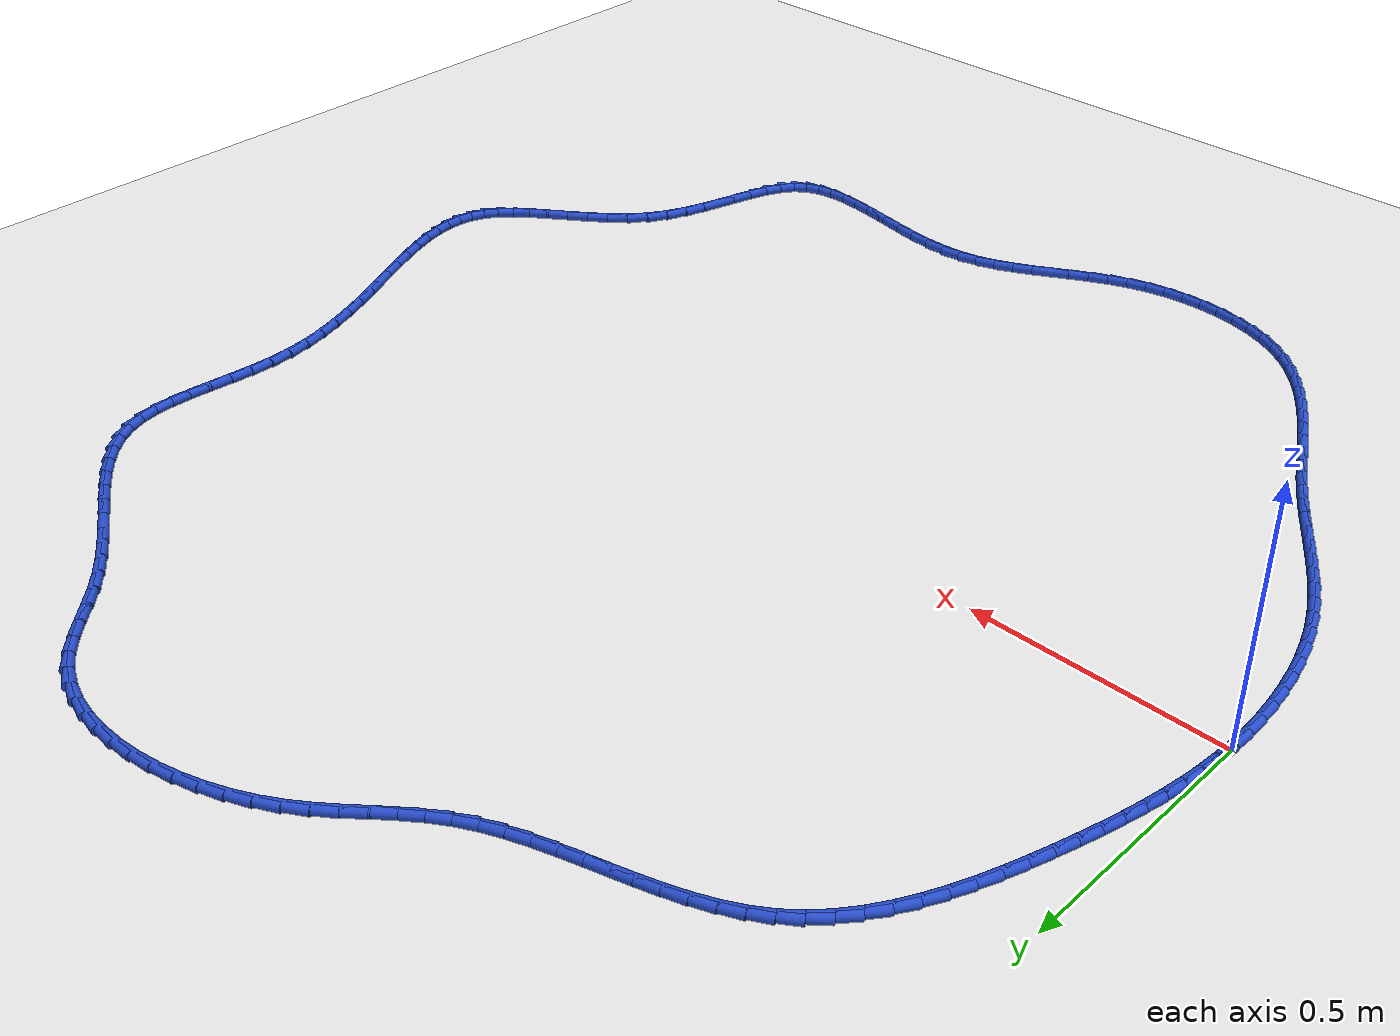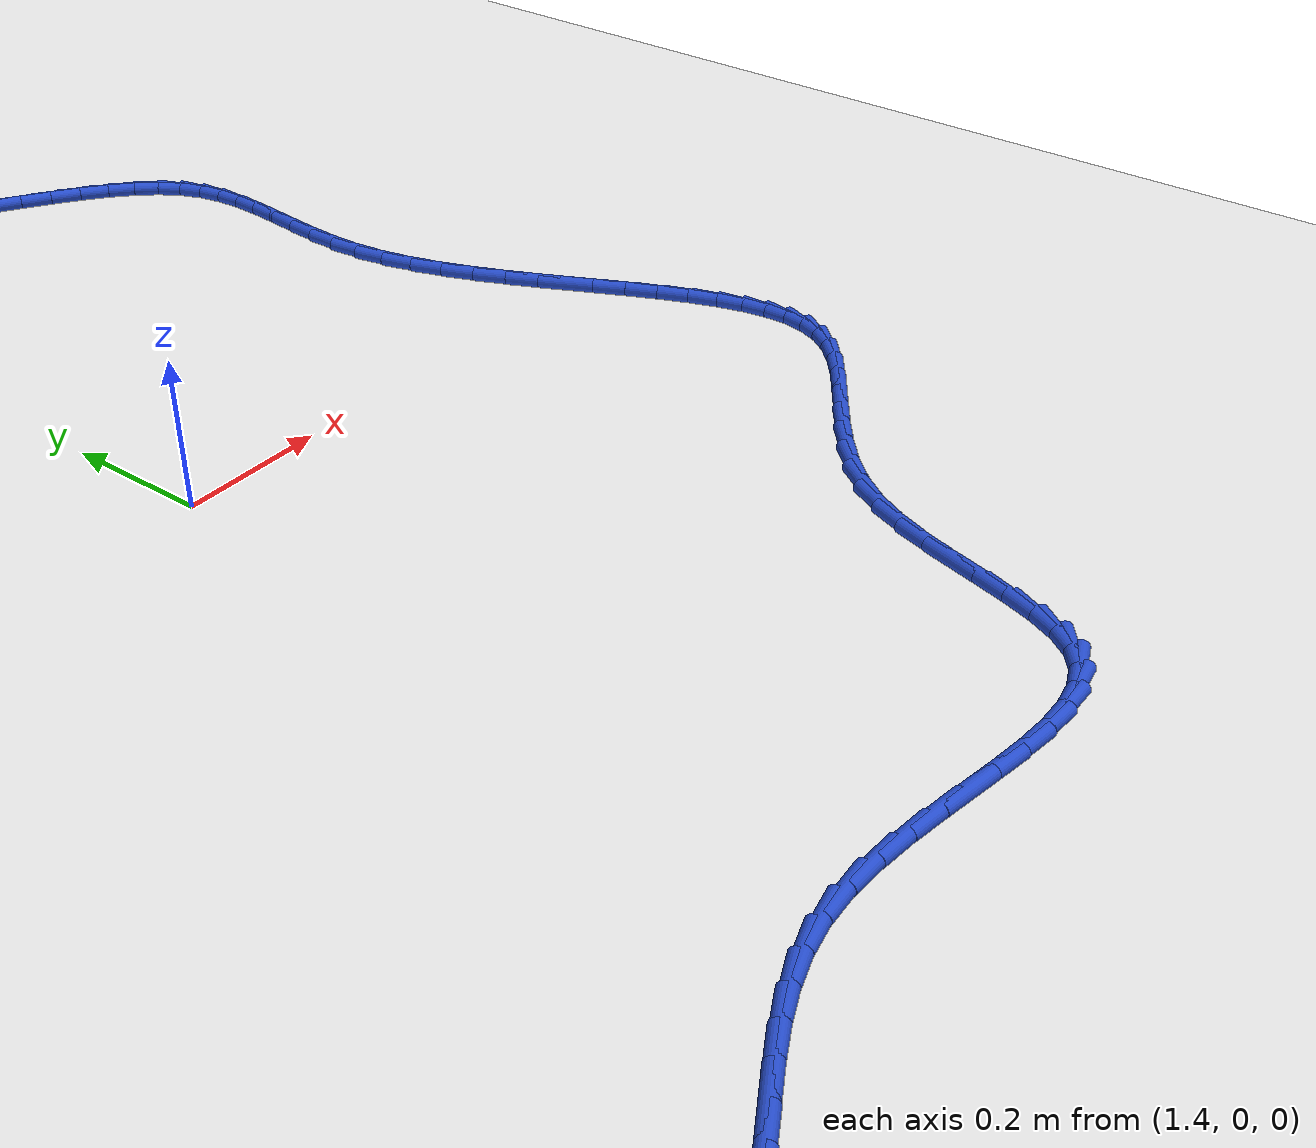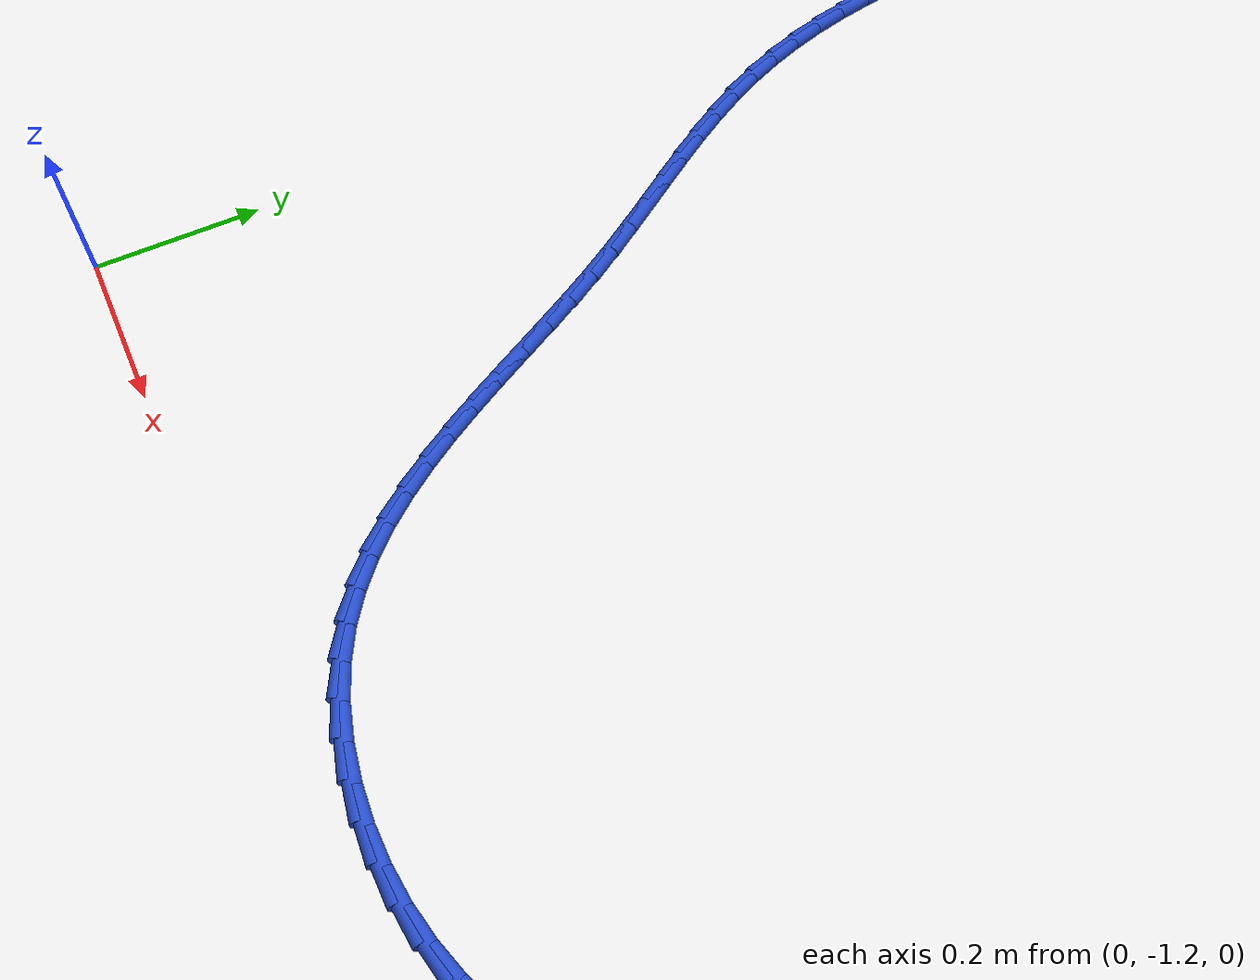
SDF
<sdf version="1.6">
 <world name="default">
  <light name="sun" type="directional">
   <pose>0 0 10 0 -0 0</pose>
   <diffuse>0.8 0.8 0.8 1</diffuse>
   <specular>0.2 0.2 0.2 1</specular>
   <attenuation>
    <range>1000</range>
    <constant>0.9</constant>
    <linear>0.01</linear>
    <quadratic>0.001</quadratic>
   </attenuation>
   <direction>-0.5 0.1 -0.9</direction>
  </light>
  <model name="ground_plane">
   <static>1</static>
   <link name="link">
    <collision name="collision">
     <geometry><plane><normal>0 0 1</normal><size>100 100</size></plane></geometry>
     <surface><friction><ode><mu>100</mu><mu2>50</mu2></ode></friction></surface>
    </collision>
    <visual name="visual">
     <cast_shadows>0</cast_shadows>
     <geometry><plane><normal>0 0 1</normal><size>100 100</size></plane></geometry>
     <material>
      <script><uri>file://media/materials/scripts/gazebo.material</uri><name>Gazebo/WhiteGlow</name></script>
     </material>
    </visual>
   </link>
  </model>
  <gravity>0 0 -9.8</gravity>
  <magnetic_field>6e-06 2.3e-05 -4.2e-05</magnetic_field>
  <atmosphere type="adiabatic"/>
  <physics name="default_physics" default="0" type="ode">
   <max_step_size>0.001</max_step_size>
   <real_time_factor>1</real_time_factor>
   <real_time_update_rate>1000</real_time_update_rate>
  </physics>
  <scene><ambient>0.4 0.4 0.4 1</ambient><background>0.7 0.7 0.7 1</background><shadows>1</shadows></scene>
  <spherical_coordinates>
   <surface_model>EARTH_WGS84</surface_model>
   <latitude_deg>0</latitude_deg>
   <longitude_deg>0</longitude_deg>
   <elevation>0</elevation>
   <heading_deg>0</heading_deg>
  </spherical_coordinates>
  <model name="line">
   <link name="link_0">
    <pose>-1.5612511283791264e-17 -2.7755575615628914e-17 0.01 0 1.57 1.5235441345351743</pose>
    <collision name="collision">
     <geometry><cylinder><radius>0.01</radius><length>0.08</length></cylinder></geometry>
    </collision>
    <visual name="visual">
     <material>
      <script><name>Gazebo/Blue</name><uri>file://media/materials/scripts/gazebo.material</uri></script>
     </material>
     <geometry><cylinder><radius>0.01</radius><length>0.08</length></cylinder></geometry>
    </visual>
   </link>
   <link name="link_1">
    <pose>0.0019587226408797564 0.04142166824580028 0.01 0 1.57 1.4812073559369945</pose>
    <collision name="collision">
     <geometry><cylinder><radius>0.01</radius><length>0.08</length></cylinder></geometry>
    </collision>
    <visual name="visual">
     <material>
      <script><name>Gazebo/Blue</name><uri>file://media/materials/scripts/gazebo.material</uri></script>
     </material>
     <geometry><cylinder><radius>0.01</radius><length>0.08</length></cylinder></geometry>
    </visual>
   </link>
   <link name="link_2">
    <pose>0.005649222530782924 0.08250508536889196 0.01 0 1.57 1.4417307428629902</pose>
    <collision name="collision">
     <geometry><cylinder><radius>0.01</radius><length>0.08</length></cylinder></geometry>
    </collision>
    <visual name="visual">
     <material>
      <script><name>Gazebo/Blue</name><uri>file://media/materials/scripts/gazebo.material</uri></script>
     </material>
     <geometry><cylinder><radius>0.01</radius><length>0.08</length></cylinder></geometry>
    </visual>
   </link>
   <link name="link_3">
    <pose>0.010949388508123768 0.1233424888013563 0.01 0 1.57 1.4054774619170307</pose>
    <collision name="collision">
     <geometry><cylinder><radius>0.01</radius><length>0.08</length></cylinder></geometry>
    </collision>
    <visual name="visual">
     <material>
      <script><name>Gazebo/Blue</name><uri>file://media/materials/scripts/gazebo.material</uri></script>
     </material>
     <geometry><cylinder><radius>0.01</radius><length>0.08</length></cylinder></geometry>
    </visual>
   </link>
   <link name="link_4">
    <pose>0.01773710941131655 0.1640261159752745 0.01 0 1.57 1.3727204085524367</pose>
    <collision name="collision">
     <geometry><cylinder><radius>0.01</radius><length>0.08</length></cylinder></geometry>
    </collision>
    <visual name="visual">
     <material>
      <script><name>Gazebo/Blue</name><uri>file://media/materials/scripts/gazebo.material</uri></script>
     </material>
     <geometry><cylinder><radius>0.01</radius><length>0.08</length></cylinder></geometry>
    </visual>
   </link>
   <link name="link_5">
    <pose>0.02589027407877554 0.20464820432272776 0.01 0 1.57 1.3436452024755448</pose>
    <collision name="collision">
     <geometry><cylinder><radius>0.01</radius><length>0.08</length></cylinder></geometry>
    </collision>
    <visual name="visual">
     <material>
      <script><name>Gazebo/Blue</name><uri>file://media/materials/scripts/gazebo.material</uri></script>
     </material>
     <geometry><cylinder><radius>0.01</radius><length>0.08</length></cylinder></geometry>
    </visual>
   </link>
   <link name="link_6">
    <pose>0.035286771348914996 0.2453009912757973 0.01 0 1.57 1.3183581355259977</pose>
    <collision name="collision">
     <geometry><cylinder><radius>0.01</radius><length>0.08</length></cylinder></geometry>
    </collision>
    <visual name="visual">
     <material>
      <script><name>Gazebo/Blue</name><uri>file://media/materials/scripts/gazebo.material</uri></script>
     </material>
     <geometry><cylinder><radius>0.01</radius><length>0.08</length></cylinder></geometry>
    </visual>
   </link>
   <link name="link_7">
    <pose>0.04580449006014919 0.28607671426656434 0.01 0 1.57 1.2968970338769943</pose>
    <collision name="collision">
     <geometry><cylinder><radius>0.01</radius><length>0.08</length></cylinder></geometry>
    </collision>
    <visual name="visual">
     <material>
      <script><name>Gazebo/Blue</name><uri>file://media/materials/scripts/gazebo.material</uri></script>
     </material>
     <geometry><cylinder><radius>0.01</radius><length>0.08</length></cylinder></geometry>
    </visual>
   </link>
   <link name="link_8">
    <pose>0.05732131905089237 0.3270676107271101 0.01 0 1.57 1.2792340524860832</pose>
    <collision name="collision">
     <geometry><cylinder><radius>0.01</radius><length>0.08</length></cylinder></geometry>
    </collision>
    <visual name="visual">
     <material>
      <script><name>Gazebo/Blue</name><uri>file://media/materials/scripts/gazebo.material</uri></script>
     </material>
     <geometry><cylinder><radius>0.01</radius><length>0.08</length></cylinder></geometry>
    </visual>
   </link>
   <link name="link_9">
    <pose>0.06971543196683273 0.3683654928058505 0.01 0 1.57 1.2624395250042082</pose>
    <collision name="collision">
     <geometry><cylinder><radius>0.01</radius><length>0.08</length></cylinder></geometry>
    </collision>
    <visual name="visual">
     <material>
      <script><name>Gazebo/Blue</name><uri>file://media/materials/scripts/gazebo.material</uri></script>
     </material>
     <geometry><cylinder><radius>0.01</radius><length>0.08</length></cylinder></geometry>
    </visual>
   </link>
   <link name="link_10">
    <pose>0.08295412861086728 0.40992908651790616 0.01 0 1.57 1.2394478316514548</pose>
    <collision name="collision">
     <geometry><cylinder><radius>0.01</radius><length>0.08</length></cylinder></geometry>
    </collision>
    <visual name="visual">
     <material>
      <script><name>Gazebo/Blue</name><uri>file://media/materials/scripts/gazebo.material</uri></script>
     </material>
     <geometry><cylinder><radius>0.01</radius><length>0.08</length></cylinder></geometry>
    </visual>
   </link>
   <link name="link_11">
    <pose>0.09721997383933727 0.45139567696258104 0.01 0 1.57 1.2088685885341466</pose>
    <collision name="collision">
     <geometry><cylinder><radius>0.01</radius><length>0.08</length></cylinder></geometry>
    </collision>
    <visual name="visual">
     <material>
      <script><name>Gazebo/Blue</name><uri>file://media/materials/scripts/gazebo.material</uri></script>
     </material>
     <geometry><cylinder><radius>0.01</radius><length>0.08</length></cylinder></geometry>
    </visual>
   </link>
   <link name="link_12">
    <pose>0.112727385505535 0.4923549852879122 0.01 0 1.57 1.1700758439015493</pose>
    <collision name="collision">
     <geometry><cylinder><radius>0.01</radius><length>0.08</length></cylinder></geometry>
    </collision>
    <visual name="visual">
     <material>
      <script><name>Gazebo/Blue</name><uri>file://media/materials/scripts/gazebo.material</uri></script>
     </material>
     <geometry><cylinder><radius>0.01</radius><length>0.08</length></cylinder></geometry>
    </visual>
   </link>
   <link name="link_13">
    <pose>0.12969078146275276 0.5323967326419369 0.01 0 1.57 1.1222036602313514</pose>
    <collision name="collision">
     <geometry><cylinder><radius>0.01</radius><length>0.08</length></cylinder></geometry>
    </collision>
    <visual name="visual">
     <material>
      <script><name>Gazebo/Blue</name><uri>file://media/materials/scripts/gazebo.material</uri></script>
     </material>
     <geometry><cylinder><radius>0.01</radius><length>0.08</length></cylinder></geometry>
    </visual>
   </link>
   <link name="link_14">
    <pose>0.14832457956428274 0.5711106401726915 0.01 0 1.57 1.064183337823634</pose>
    <collision name="collision">
     <geometry><cylinder><radius>0.01</radius><length>0.08</length></cylinder></geometry>
    </collision>
    <visual name="visual">
     <material>
      <script><name>Gazebo/Blue</name><uri>file://media/materials/scripts/gazebo.material</uri></script>
     </material>
     <geometry><cylinder><radius>0.01</radius><length>0.08</length></cylinder></geometry>
    </visual>
   </link>
   <link name="link_15">
    <pose>0.1688431976634173 0.6080864290282142 0.01 0 1.57 0.9948238684890548</pose>
    <collision name="collision">
     <geometry><cylinder><radius>0.01</radius><length>0.08</length></cylinder></geometry>
    </collision>
    <visual name="visual">
     <material>
      <script><name>Gazebo/Blue</name><uri>file://media/materials/scripts/gazebo.material</uri></script>
     </material>
     <geometry><cylinder><radius>0.01</radius><length>0.08</length></cylinder></geometry>
    </visual>
   </link>
   <link name="link_16">
    <pose>0.1914610536134488 0.6429138203565417 0.01 0 1.57 0.9129737837188721</pose>
    <collision name="collision">
     <geometry><cylinder><radius>0.01</radius><length>0.08</length></cylinder></geometry>
    </collision>
    <visual name="visual">
     <material>
      <script><name>Gazebo/Blue</name><uri>file://media/materials/scripts/gazebo.material</uri></script>
     </material>
     <geometry><cylinder><radius>0.01</radius><length>0.08</length></cylinder></geometry>
    </visual>
   </link>
   <link name="link_17">
    <pose>0.2163925652676694 0.6751825353057106 0.01 0 1.57 0.8178074552991463</pose>
    <collision name="collision">
     <geometry><cylinder><radius>0.01</radius><length>0.08</length></cylinder></geometry>
    </collision>
    <visual name="visual">
     <material>
      <script><name>Gazebo/Blue</name><uri>file://media/materials/scripts/gazebo.material</uri></script>
     </material>
     <geometry><cylinder><radius>0.01</radius><length>0.08</length></cylinder></geometry>
    </visual>
   </link>
   <link name="link_18">
    <pose>0.24385215047937137 0.7044822950237585 0.01 0 1.57 0.7092593948241007</pose>
    <collision name="collision">
     <geometry><cylinder><radius>0.01</radius><length>0.08</length></cylinder></geometry>
    </collision>
    <visual name="visual">
     <material>
      <script><name>Gazebo/Blue</name><uri>file://media/materials/scripts/gazebo.material</uri></script>
     </material>
     <geometry><cylinder><radius>0.01</radius><length>0.08</length></cylinder></geometry>
    </visual>
   </link>
   <link name="link_19">
    <pose>0.2740541610401618 0.7304029207470495 0.01 0 1.57 0.5948056163354342</pose>
    <collision name="collision">
     <geometry><cylinder><radius>0.01</radius><length>0.08</length></cylinder></geometry>
    </collision>
    <visual name="visual">
     <material>
      <script><name>Gazebo/Blue</name><uri>file://media/materials/scripts/gazebo.material</uri></script>
     </material>
     <geometry><cylinder><radius>0.01</radius><length>0.08</length></cylinder></geometry>
    </visual>
   </link>
   <link name="link_20">
    <pose>0.3070752088580482 0.7527429197977387 0.01 0 1.57 0.4960526257668971</pose>
    <collision name="collision">
     <geometry><cylinder><radius>0.01</radius><length>0.08</length></cylinder></geometry>
    </collision>
    <visual name="visual">
     <material>
      <script><name>Gazebo/Blue</name><uri>file://media/materials/scripts/gazebo.material</uri></script>
     </material>
     <geometry><cylinder><radius>0.01</radius><length>0.08</length></cylinder></geometry>
    </visual>
   </link>
   <link name="link_21">
    <pose>0.34256403859086515 0.7719490499490717 0.01 0 1.57 0.4175085380684355</pose>
    <collision name="collision">
     <geometry><cylinder><radius>0.01</radius><length>0.08</length></cylinder></geometry>
    </collision>
    <visual name="visual">
     <material>
      <script><name>Gazebo/Blue</name><uri>file://media/materials/scripts/gazebo.material</uri></script>
     </material>
     <geometry><cylinder><radius>0.01</radius><length>0.08</length></cylinder></geometry>
    </visual>
   </link>
   <link name="link_22">
    <pose>0.38008655859361185 0.7885935720845658 0.01 0 1.57 0.35842059746714927</pose>
    <collision name="collision">
     <geometry><cylinder><radius>0.01</radius><length>0.08</length></cylinder></geometry>
    </collision>
    <visual name="visual">
     <material>
      <script><name>Gazebo/Blue</name><uri>file://media/materials/scripts/gazebo.material</uri></script>
     </material>
     <geometry><cylinder><radius>0.01</radius><length>0.08</length></cylinder></geometry>
    </visual>
   </link>
   <link name="link_23">
    <pose>0.4192086772212879 0.8032487470877382 0.01 0 1.57 0.3174750009113075</pose>
    <collision name="collision">
     <geometry><cylinder><radius>0.01</radius><length>0.08</length></cylinder></geometry>
    </collision>
    <visual name="visual">
     <material>
      <script><name>Gazebo/Blue</name><uri>file://media/materials/scripts/gazebo.material</uri></script>
     </material>
     <geometry><cylinder><radius>0.01</radius><length>0.08</length></cylinder></geometry>
    </visual>
   </link>
   <link name="link_24">
    <pose>0.45949630282889253 0.8164868358421056 0.01 0 1.57 0.2934138089287271</pose>
    <collision name="collision">
     <geometry><cylinder><radius>0.01</radius><length>0.08</length></cylinder></geometry>
    </collision>
    <visual name="visual">
     <material>
      <script><name>Gazebo/Blue</name><uri>file://media/materials/scripts/gazebo.material</uri></script>
     </material>
     <geometry><cylinder><radius>0.01</radius><length>0.08</length></cylinder></geometry>
    </visual>
   </link>
   <link name="link_25">
    <pose>0.5005153437714251 0.8288800992311849 0.01 0 1.57 0.2853568750488114</pose>
    <collision name="collision">
     <geometry><cylinder><radius>0.01</radius><length>0.08</length></cylinder></geometry>
    </collision>
    <visual name="visual">
     <material>
      <script><name>Gazebo/Blue</name><uri>file://media/materials/scripts/gazebo.material</uri></script>
     </material>
     <geometry><cylinder><radius>0.01</radius><length>0.08</length></cylinder></geometry>
    </visual>
   </link>
   <link name="link_26">
    <pose>0.5418317084038852 0.8410007981384933 0.01 0 1.57 0.2929380370500118</pose>
    <collision name="collision">
     <geometry><cylinder><radius>0.01</radius><length>0.08</length></cylinder></geometry>
    </collision>
    <visual name="visual">
     <material>
      <script><name>Gazebo/Blue</name><uri>file://media/materials/scripts/gazebo.material</uri></script>
     </material>
     <geometry><cylinder><radius>0.01</radius><length>0.08</length></cylinder></geometry>
    </visual>
   </link>
   <link name="link_27">
    <pose>0.5830113050812714 0.8534211934475472 0.01 0 1.57 0.3163355165066644</pose>
    <collision name="collision">
     <geometry><cylinder><radius>0.01</radius><length>0.08</length></cylinder></geometry>
    </collision>
    <visual name="visual">
     <material>
      <script><name>Gazebo/Blue</name><uri>file://media/materials/scripts/gazebo.material</uri></script>
     </material>
     <geometry><cylinder><radius>0.01</radius><length>0.08</length></cylinder></geometry>
    </visual>
   </link>
   <link name="link_28">
    <pose>0.6236200421585838 0.8667135460418643 0.01 0 1.57 0.3562258292247421</pose>
    <collision name="collision">
     <geometry><cylinder><radius>0.01</radius><length>0.08</length></cylinder></geometry>
    </collision>
    <visual name="visual">
     <material>
      <script><name>Gazebo/Blue</name><uri>file://media/materials/scripts/gazebo.material</uri></script>
     </material>
     <geometry><cylinder><radius>0.01</radius><length>0.08</length></cylinder></geometry>
    </visual>
   </link>
   <link name="link_29">
    <pose>0.6632238279908214 0.8814501168049611 0.01 0 1.57 0.413640812660089</pose>
    <collision name="collision">
     <geometry><cylinder><radius>0.01</radius><length>0.08</length></cylinder></geometry>
    </collision>
    <visual name="visual">
     <material>
      <script><name>Gazebo/Blue</name><uri>file://media/materials/scripts/gazebo.material</uri></script>
     </material>
     <geometry><cylinder><radius>0.01</radius><length>0.08</length></cylinder></geometry>
    </visual>
   </link>
   <link name="link_30">
    <pose>0.7013885709329837 0.8982031666203546 0.01 0 1.57 0.48966263523068054</pose>
    <collision name="collision">
     <geometry><cylinder><radius>0.01</radius><length>0.08</length></cylinder></geometry>
    </collision>
    <visual name="visual">
     <material>
      <script><name>Gazebo/Blue</name><uri>file://media/materials/scripts/gazebo.material</uri></script>
     </material>
     <geometry><cylinder><radius>0.01</radius><length>0.08</length></cylinder></geometry>
    </visual>
   </link>
   <link name="link_31">
    <pose>0.7376801793400698 0.9175449563715617 0.01 0 1.57 0.5793938275352636</pose>
    <collision name="collision">
     <geometry><cylinder><radius>0.01</radius><length>0.08</length></cylinder></geometry>
    </collision>
    <visual name="visual">
     <material>
      <script><name>Gazebo/Blue</name><uri>file://media/materials/scripts/gazebo.material</uri></script>
     </material>
     <geometry><cylinder><radius>0.01</radius><length>0.08</length></cylinder></geometry>
    </visual>
   </link>
   <link name="link_32">
    <pose>0.7718120637004536 0.9398775310171754 0.01 0 1.57 0.6499337032496447</pose>
    <collision name="collision">
     <geometry><cylinder><radius>0.01</radius><length>0.08</length></cylinder></geometry>
    </collision>
    <visual name="visual">
     <material>
      <script><name>Gazebo/Blue</name><uri>file://media/materials/scripts/gazebo.material</uri></script>
     </material>
     <geometry><cylinder><radius>0.01</radius><length>0.08</length></cylinder></geometry>
    </visual>
   </link>
   <link name="link_33">
    <pose>0.8043550702523262 0.9646134635950826 0.01 0 1.57 0.6885315111517385</pose>
    <collision name="collision">
     <geometry><cylinder><radius>0.01</radius><length>0.08</length></cylinder></geometry>
    </collision>
    <visual name="visual">
     <material>
      <script><name>Gazebo/Blue</name><uri>file://media/materials/scripts/gazebo.material</uri></script>
     </material>
     <geometry><cylinder><radius>0.01</radius><length>0.08</length></cylinder></geometry>
    </visual>
   </link>
   <link name="link_34">
    <pose>0.8361890696538092 0.9908087161826402 0.01 0 1.57 0.6954569006285427</pose>
    <collision name="collision">
     <geometry><cylinder><radius>0.01</radius><length>0.08</length></cylinder></geometry>
    </collision>
    <visual name="visual">
     <material>
      <script><name>Gazebo/Blue</name><uri>file://media/materials/scripts/gazebo.material</uri></script>
     </material>
     <geometry><cylinder><radius>0.01</radius><length>0.08</length></cylinder></geometry>
    </visual>
   </link>
   <link name="link_35">
    <pose>0.8681943453729905 1.0175187744788063 0.01 0 1.57 0.6716877842707996</pose>
    <collision name="collision">
     <geometry><cylinder><radius>0.01</radius><length>0.08</length></cylinder></geometry>
    </collision>
    <visual name="visual">
     <material>
      <script><name>Gazebo/Blue</name><uri>file://media/materials/scripts/gazebo.material</uri></script>
     </material>
     <geometry><cylinder><radius>0.01</radius><length>0.08</length></cylinder></geometry>
    </visual>
   </link>
   <link name="link_36">
    <pose>0.9012511808779582 1.0437991241825397 0.01 0 1.57 0.6186240878455893</pose>
    <collision name="collision">
     <geometry><cylinder><radius>0.01</radius><length>0.08</length></cylinder></geometry>
    </collision>
    <visual name="visual">
     <material>
      <script><name>Gazebo/Blue</name><uri>file://media/materials/scripts/gazebo.material</uri></script>
     </material>
     <geometry><cylinder><radius>0.01</radius><length>0.08</length></cylinder></geometry>
    </visual>
   </link>
   <link name="link_37">
    <pose>0.9362398596368002 1.0687052509927988 0.01 0 1.57 0.5428938042867804</pose>
    <collision name="collision">
     <geometry><cylinder><radius>0.01</radius><length>0.08</length></cylinder></geometry>
    </collision>
    <visual name="visual">
     <material>
      <script><name>Gazebo/Blue</name><uri>file://media/materials/scripts/gazebo.material</uri></script>
     </material>
     <geometry><cylinder><radius>0.01</radius><length>0.08</length></cylinder></geometry>
    </visual>
   </link>
   <link name="link_38">
    <pose>0.9738482978249657 1.0913970567296392 0.01 0 1.57 0.46622374881692324</pose>
    <collision name="collision">
     <geometry><cylinder><radius>0.01</radius><length>0.08</length></cylinder></geometry>
    </collision>
    <visual name="visual">
     <material>
      <script><name>Gazebo/Blue</name><uri>file://media/materials/scripts/gazebo.material</uri></script>
     </material>
     <geometry><cylinder><radius>0.01</radius><length>0.08</length></cylinder></geometry>
    </visual>
   </link>
   <link name="link_39">
    <pose>1.0138537237460024 1.1115287605880206 0.01 0 1.57 0.39294533319013003</pose>
    <collision name="collision">
     <geometry><cylinder><radius>0.01</radius><length>0.08</length></cylinder></geometry>
    </collision>
    <visual name="visual">
     <material>
      <script><name>Gazebo/Blue</name><uri>file://media/materials/scripts/gazebo.material</uri></script>
     </material>
     <geometry><cylinder><radius>0.01</radius><length>0.08</length></cylinder></geometry>
    </visual>
   </link>
   <link name="link_40">
    <pose>1.055764140451307 1.1289007160466766 0.01 0 1.57 0.32115752640766104</pose>
    <collision name="collision">
     <geometry><cylinder><radius>0.01</radius><length>0.08</length></cylinder></geometry>
    </collision>
    <visual name="visual">
     <material>
      <script><name>Gazebo/Blue</name><uri>file://media/materials/scripts/gazebo.material</uri></script>
     </material>
     <geometry><cylinder><radius>0.01</radius><length>0.08</length></cylinder></geometry>
    </visual>
   </link>
   <link name="link_41">
    <pose>1.0990875106862608 1.1433132984622671 0.01 0 1.57 0.24906964289258188</pose>
    <collision name="collision">
     <geometry><cylinder><radius>0.01</radius><length>0.08</length></cylinder></geometry>
    </collision>
    <visual name="visual">
     <material>
      <script><name>Gazebo/Blue</name><uri>file://media/materials/scripts/gazebo.material</uri></script>
     </material>
     <geometry><cylinder><radius>0.01</radius><length>0.08</length></cylinder></geometry>
    </visual>
   </link>
   <link name="link_42">
    <pose>1.1433317971962451 1.154566883191454 0.01 0 1.57 0.17492102681269955</pose>
    <collision name="collision">
     <geometry><cylinder><radius>0.01</radius><length>0.08</length></cylinder></geometry>
    </collision>
    <visual name="visual">
     <material>
      <script><name>Gazebo/Blue</name><uri>file://media/materials/scripts/gazebo.material</uri></script>
     </material>
     <geometry><cylinder><radius>0.01</radius><length>0.08</length></cylinder></geometry>
    </visual>
   </link>
   <link name="link_43">
    <pose>1.1880049627266416 1.1624618455908977 0.01 0 1.57 0.0969094420745964</pose>
    <collision name="collision">
     <geometry><cylinder><radius>0.01</radius><length>0.08</length></cylinder></geometry>
    </collision>
    <visual name="visual">
     <material>
      <script><name>Gazebo/Blue</name><uri>file://media/materials/scripts/gazebo.material</uri></script>
     </material>
     <geometry><cylinder><radius>0.01</radius><length>0.08</length></cylinder></geometry>
    </visual>
   </link>
   <link name="link_44">
    <pose>1.2326149700228315 1.1667985610172593 0.01 0 1.57 0.01313841733789783</pose>
    <collision name="collision">
     <geometry><cylinder><radius>0.01</radius><length>0.08</length></cylinder></geometry>
    </collision>
    <visual name="visual">
     <material>
      <script><name>Gazebo/Blue</name><uri>file://media/materials/scripts/gazebo.material</uri></script>
     </material>
     <geometry><cylinder><radius>0.01</radius><length>0.08</length></cylinder></geometry>
    </visual>
   </link>
   <link name="link_45">
    <pose>1.2766697818301966 1.1673774048271992 0.01 0 1.57 -0.07839844966000052</pose>
    <collision name="collision">
     <geometry><cylinder><radius>0.01</radius><length>0.08</length></cylinder></geometry>
    </collision>
    <visual name="visual">
     <material>
      <script><name>Gazebo/Blue</name><uri>file://media/materials/scripts/gazebo.material</uri></script>
     </material>
     <geometry><cylinder><radius>0.01</radius><length>0.08</length></cylinder></geometry>
    </visual>
   </link>
   <link name="link_46">
    <pose>1.3196773608941181 1.1639987523773787 0.01 0 1.57 -0.17976201178281492</pose>
    <collision name="collision">
     <geometry><cylinder><radius>0.01</radius><length>0.08</length></cylinder></geometry>
    </collision>
    <visual name="visual">
     <material>
      <script><name>Gazebo/Blue</name><uri>file://media/materials/scripts/gazebo.material</uri></script>
     </material>
     <geometry><cylinder><radius>0.01</radius><length>0.08</length></cylinder></geometry>
    </visual>
   </link>
   <link name="link_47">
    <pose>1.3611456699599778 1.1564629790244585 0.01 0 1.57 -0.29288496934135305</pose>
    <collision name="collision">
     <geometry><cylinder><radius>0.01</radius><length>0.08</length></cylinder></geometry>
    </collision>
    <visual name="visual">
     <material>
      <script><name>Gazebo/Blue</name><uri>file://media/materials/scripts/gazebo.material</uri></script>
     </material>
     <geometry><cylinder><radius>0.01</radius><length>0.08</length></cylinder></geometry>
    </visual>
   </link>
   <link name="link_48">
    <pose>1.4005826717731562 1.1445704601250994 0.01 0 1.57 -0.41919255714978215</pose>
    <collision name="collision">
     <geometry><cylinder><radius>0.01</radius><length>0.08</length></cylinder></geometry>
    </collision>
    <visual name="visual">
     <material>
      <script><name>Gazebo/Blue</name><uri>file://media/materials/scripts/gazebo.material</uri></script>
     </material>
     <geometry><cylinder><radius>0.01</radius><length>0.08</length></cylinder></geometry>
    </visual>
   </link>
   <link name="link_49">
    <pose>1.437496329079036 1.128121571035963 0.01 0 1.57 -0.5583029167495953</pose>
    <collision name="collision">
     <geometry><cylinder><radius>0.01</radius><length>0.08</length></cylinder></geometry>
    </collision>
    <visual name="visual">
     <material>
      <script><name>Gazebo/Blue</name><uri>file://media/materials/scripts/gazebo.material</uri></script>
     </material>
     <geometry><cylinder><radius>0.01</radius><length>0.08</length></cylinder></geometry>
    </visual>
   </link>
   <link name="link_50">
    <pose>1.4714160359522916 1.1069357326519556 0.01 0 1.57 -0.6841987360473872</pose>
    <collision name="collision">
     <geometry><cylinder><radius>0.01</radius><length>0.08</length></cylinder></geometry>
    </collision>
    <visual name="visual">
     <material>
      <script><name>Gazebo/Blue</name><uri>file://media/materials/scripts/gazebo.material</uri></script>
     </material>
     <geometry><cylinder><radius>0.01</radius><length>0.08</length></cylinder></geometry>
    </visual>
   </link>
   <link name="link_51">
    <pose>1.5026123953724473 1.0814910614791031 0.01 0 1.57 -0.764009676580501</pose>
    <collision name="collision">
     <geometry><cylinder><radius>0.01</radius><length>0.08</length></cylinder></geometry>
    </collision>
    <visual name="visual">
     <material>
      <script><name>Gazebo/Blue</name><uri>file://media/materials/scripts/gazebo.material</uri></script>
     </material>
     <geometry><cylinder><radius>0.01</radius><length>0.08</length></cylinder></geometry>
    </visual>
   </link>
   <link name="link_52">
    <pose>1.5322688208373172 1.0530768681122282 0.01 0 1.57 -0.7969854230017098</pose>
    <collision name="collision">
     <geometry><cylinder><radius>0.01</radius><length>0.08</length></cylinder></geometry>
    </collision>
    <visual name="visual">
     <material>
      <script><name>Gazebo/Blue</name><uri>file://media/materials/scripts/gazebo.material</uri></script>
     </material>
     <geometry><cylinder><radius>0.01</radius><length>0.08</length></cylinder></geometry>
    </visual>
   </link>
   <link name="link_53">
    <pose>1.5616249447338104 1.0230324236030077 0.01 0 1.57 -0.7860573964405503</pose>
    <collision name="collision">
     <geometry><cylinder><radius>0.01</radius><length>0.08</length></cylinder></geometry>
    </collision>
    <visual name="visual">
     <material>
      <script><name>Gazebo/Blue</name><uri>file://media/materials/scripts/gazebo.material</uri></script>
     </material>
     <geometry><cylinder><radius>0.01</radius><length>0.08</length></cylinder></geometry>
    </visual>
   </link>
   <link name="link_54">
    <pose>1.591920399448836 0.9926969990031153 0.01 0 1.57 -0.7341413859010629</pose>
    <collision name="collision">
     <geometry><cylinder><radius>0.01</radius><length>0.08</length></cylinder></geometry>
    </collision>
    <visual name="visual">
     <material>
      <script><name>Gazebo/Blue</name><uri>file://media/materials/scripts/gazebo.material</uri></script>
     </material>
     <geometry><cylinder><radius>0.01</radius><length>0.08</length></cylinder></geometry>
    </visual>
   </link>
   <link name="link_55">
    <pose>1.6243846077212396 0.9634011856337734 0.01 0 1.57 -0.6647828148002256</pose>
    <collision name="collision">
     <geometry><cylinder><radius>0.01</radius><length>0.08</length></cylinder></geometry>
    </collision>
    <visual name="visual">
     <material>
      <script><name>Gazebo/Blue</name><uri>file://media/materials/scripts/gazebo.material</uri></script>
     </material>
     <geometry><cylinder><radius>0.01</radius><length>0.08</length></cylinder></geometry>
    </visual>
   </link>
   <link name="link_56">
    <pose>1.6595228400960749 0.9358599369597133 0.01 0 1.57 -0.6124754038024182</pose>
    <collision name="collision">
     <geometry><cylinder><radius>0.01</radius><length>0.08</length></cylinder></geometry>
    </collision>
    <visual name="visual">
     <material>
      <script><name>Gazebo/Blue</name><uri>file://media/materials/scripts/gazebo.material</uri></script>
     </material>
     <geometry><cylinder><radius>0.01</radius><length>0.08</length></cylinder></geometry>
    </visual>
   </link>
   <link name="link_57">
    <pose>1.6966485909951337 0.9097750181901658 0.01 0 1.57 -0.5785015639301634</pose>
    <collision name="collision">
     <geometry><cylinder><radius>0.01</radius><length>0.08</length></cylinder></geometry>
    </collision>
    <visual name="visual">
     <material>
      <script><name>Gazebo/Blue</name><uri>file://media/materials/scripts/gazebo.material</uri></script>
     </material>
     <geometry><cylinder><radius>0.01</radius><length>0.08</length></cylinder></geometry>
    </visual>
   </link>
   <link name="link_58">
    <pose>1.7349642807448902 0.8847537649123323 0.01 0 1.57 -0.5615240338880346</pose>
    <collision name="collision">
     <geometry><cylinder><radius>0.01</radius><length>0.08</length></cylinder></geometry>
    </collision>
    <visual name="visual">
     <material>
      <script><name>Gazebo/Blue</name><uri>file://media/materials/scripts/gazebo.material</uri></script>
     </material>
     <geometry><cylinder><radius>0.01</radius><length>0.08</length></cylinder></geometry>
    </visual>
   </link>
   <link name="link_59">
    <pose>1.7736723296718186 0.8604035127134135 0.01 0 1.57 -0.5610857824687269</pose>
    <collision name="collision">
     <geometry><cylinder><radius>0.01</radius><length>0.08</length></cylinder></geometry>
    </collision>
    <visual name="visual">
     <material>
      <script><name>Gazebo/Blue</name><uri>file://media/materials/scripts/gazebo.material</uri></script>
     </material>
     <geometry><cylinder><radius>0.01</radius><length>0.08</length></cylinder></geometry>
    </visual>
   </link>
   <link name="link_60">
    <pose>1.8119751581023948 0.8363315971806116 0.01 0 1.57 -0.5777236378943515</pose>
    <collision name="collision">
     <geometry><cylinder><radius>0.01</radius><length>0.08</length></cylinder></geometry>
    </collision>
    <visual name="visual">
     <material>
      <script><name>Gazebo/Blue</name><uri>file://media/materials/scripts/gazebo.material</uri></script>
     </material>
     <geometry><cylinder><radius>0.01</radius><length>0.08</length></cylinder></geometry>
    </visual>
   </link>
   <link name="link_61">
    <pose>1.8490751863630932 0.8121453539011263 0.01 0 1.57 -0.6130831567668751</pose>
    <collision name="collision">
     <geometry><cylinder><radius>0.01</radius><length>0.08</length></cylinder></geometry>
    </collision>
    <visual name="visual">
     <material>
      <script><name>Gazebo/Blue</name><uri>file://media/materials/scripts/gazebo.material</uri></script>
     </material>
     <geometry><cylinder><radius>0.01</radius><length>0.08</length></cylinder></geometry>
    </visual>
   </link>
   <link name="link_62">
    <pose>1.8841748347803877 0.7874521184621599 0.01 0 1.57 -0.6700331723719222</pose>
    <collision name="collision">
     <geometry><cylinder><radius>0.01</radius><length>0.08</length></cylinder></geometry>
    </collision>
    <visual name="visual">
     <material>
      <script><name>Gazebo/Blue</name><uri>file://media/materials/scripts/gazebo.material</uri></script>
     </material>
     <geometry><cylinder><radius>0.01</radius><length>0.08</length></cylinder></geometry>
    </visual>
   </link>
   <link name="link_63">
    <pose>1.9164765236807548 0.7618592264509132 0.01 0 1.57 -0.7526541220119248</pose>
    <collision name="collision">
     <geometry><cylinder><radius>0.01</radius><length>0.08</length></cylinder></geometry>
    </collision>
    <visual name="visual">
     <material>
      <script><name>Gazebo/Blue</name><uri>file://media/materials/scripts/gazebo.material</uri></script>
     </material>
     <geometry><cylinder><radius>0.01</radius><length>0.08</length></cylinder></geometry>
    </visual>
   </link>
   <link name="link_64">
    <pose>1.9451826733906683 0.7349740134545877 0.01 0 1.57 -0.8657262196260628</pose>
    <collision name="collision">
     <geometry><cylinder><radius>0.01</radius><length>0.08</length></cylinder></geometry>
    </collision>
    <visual name="visual">
     <material>
      <script><name>Gazebo/Blue</name><uri>file://media/materials/scripts/gazebo.material</uri></script>
     </material>
     <geometry><cylinder><radius>0.01</radius><length>0.08</length></cylinder></geometry>
    </visual>
   </link>
   <link name="link_65">
    <pose>1.9694957042366024 0.7064038150603841 0.01 0 1.57 -1.0129616439397218</pose>
    <collision name="collision">
     <geometry><cylinder><radius>0.01</radius><length>0.08</length></cylinder></geometry>
    </collision>
    <visual name="visual">
     <material>
      <script><name>Gazebo/Blue</name><uri>file://media/materials/scripts/gazebo.material</uri></script>
     </material>
     <geometry><cylinder><radius>0.01</radius><length>0.08</length></cylinder></geometry>
    </visual>
   </link>
   <link name="link_66">
    <pose>1.9886180365450326 0.6757559668555035 0.01 0 1.57 -1.192933921805183</pose>
    <collision name="collision">
     <geometry><cylinder><radius>0.01</radius><length>0.08</length></cylinder></geometry>
    </collision>
    <visual name="visual">
     <material>
      <script><name>Gazebo/Blue</name><uri>file://media/materials/scripts/gazebo.material</uri></script>
     </material>
     <geometry><cylinder><radius>0.01</radius><length>0.08</length></cylinder></geometry>
    </visual>
   </link>
   <link name="link_67">
    <pose>2.0017624751888983 0.6426412300228792 0.01 0 1.57 -1.3738185705847812</pose>
    <collision name="collision">
     <geometry><cylinder><radius>0.01</radius><length>0.08</length></cylinder></geometry>
    </collision>
    <visual name="visual">
     <material>
      <script><name>Gazebo/Blue</name><uri>file://media/materials/scripts/gazebo.material</uri></script>
     </material>
     <geometry><cylinder><radius>0.01</radius><length>0.08</length></cylinder></geometry>
    </visual>
   </link>
   <link name="link_68">
    <pose>2.0088916568504382 0.6069177160417845 0.01 0 1.57 -1.5099692431528025</pose>
    <collision name="collision">
     <geometry><cylinder><radius>0.01</radius><length>0.08</length></cylinder></geometry>
    </collision>
    <visual name="visual">
     <material>
      <script><name>Gazebo/Blue</name><uri>file://media/materials/scripts/gazebo.material</uri></script>
     </material>
     <geometry><cylinder><radius>0.01</radius><length>0.08</length></cylinder></geometry>
    </visual>
   </link>
   <link name="link_69">
    <pose>2.011209874581328 0.5688531270051806 0.01 0 1.57 1.5415825518406643</pose>
    <collision name="collision">
     <geometry><cylinder><radius>0.01</radius><length>0.08</length></cylinder></geometry>
    </collision>
    <visual name="visual">
     <material>
      <script><name>Gazebo/Blue</name><uri>file://media/materials/scripts/gazebo.material</uri></script>
     </material>
     <geometry><cylinder><radius>0.01</radius><length>0.08</length></cylinder></geometry>
    </visual>
   </link>
   <link name="link_70">
    <pose>2.0100380840840764 0.5287536490245757 0.01 0 1.57 1.4910948927993597</pose>
    <collision name="collision">
     <geometry><cylinder><radius>0.01</radius><length>0.08</length></cylinder></geometry>
    </collision>
    <visual name="visual">
     <material>
      <script><name>Gazebo/Blue</name><uri>file://media/materials/scripts/gazebo.material</uri></script>
     </material>
     <geometry><cylinder><radius>0.01</radius><length>0.08</length></cylinder></geometry>
    </visual>
   </link>
   <link name="link_71">
    <pose>2.0066972410611967 0.4869254682114772 0.01 0 1.57 1.474244934203311</pose>
    <collision name="collision">
     <geometry><cylinder><radius>0.01</radius><length>0.08</length></cylinder></geometry>
    </collision>
    <visual name="visual">
     <material>
      <script><name>Gazebo/Blue</name><uri>file://media/materials/scripts/gazebo.material</uri></script>
     </material>
     <geometry><cylinder><radius>0.01</radius><length>0.08</length></cylinder></geometry>
    </visual>
   </link>
   <link name="link_72">
    <pose>2.0025083012151996 0.44367477067739447 0.01 0 1.57 1.4872336533153059</pose>
    <collision name="collision">
     <geometry><cylinder><radius>0.01</radius><length>0.08</length></cylinder></geometry>
    </collision>
    <visual name="visual">
     <material>
      <script><name>Gazebo/Blue</name><uri>file://media/materials/scripts/gazebo.material</uri></script>
     </material>
     <geometry><cylinder><radius>0.01</radius><length>0.08</length></cylinder></geometry>
    </visual>
   </link>
   <link name="link_73">
    <pose>1.9987922202485966 0.39930774253383516 0.01 0 1.57 1.528272470863807</pose>
    <collision name="collision">
     <geometry><cylinder><radius>0.01</radius><length>0.08</length></cylinder></geometry>
    </collision>
    <visual name="visual">
     <material>
      <script><name>Gazebo/Blue</name><uri>file://media/materials/scripts/gazebo.material</uri></script>
     </material>
     <geometry><cylinder><radius>0.01</radius><length>0.08</length></cylinder></geometry>
    </visual>
   </link>
   <link name="link_74">
    <pose>1.9968699538638994 0.3541305698923073 0.01 0 1.57 -1.5446972986207361</pose>
    <collision name="collision">
     <geometry><cylinder><radius>0.01</radius><length>0.08</length></cylinder></geometry>
    </collision>
    <visual name="visual">
     <material>
      <script><name>Gazebo/Blue</name><uri>file://media/materials/scripts/gazebo.material</uri></script>
     </material>
     <geometry><cylinder><radius>0.01</radius><length>0.08</length></cylinder></geometry>
    </visual>
   </link>
   <link name="link_75">
    <pose>1.9980624577636186 0.30844943886431964 0.01 0 1.57 -1.451494894429507</pose>
    <collision name="collision">
     <geometry><cylinder><radius>0.01</radius><length>0.08</length></cylinder></geometry>
    </collision>
    <visual name="visual">
     <material>
      <script><name>Gazebo/Blue</name><uri>file://media/materials/scripts/gazebo.material</uri></script>
     </material>
     <geometry><cylinder><radius>0.01</radius><length>0.08</length></cylinder></geometry>
    </visual>
   </link>
   <link name="link_76">
    <pose>2.0035632578234095 0.2625599819278947 0.01 0 1.57 -1.3608356118671094</pose>
    <collision name="collision">
     <geometry><cylinder><radius>0.01</radius><length>0.08</length></cylinder></geometry>
    </collision>
    <visual name="visual">
     <material>
      <script><name>Gazebo/Blue</name><uri>file://media/materials/scripts/gazebo.material</uri></script>
     </material>
     <geometry><cylinder><radius>0.01</radius><length>0.08</length></cylinder></geometry>
    </visual>
   </link>
   <link name="link_77">
    <pose>2.0133453008955464 0.21665674420991735 0.01 0 1.57 -1.2869007687631921</pose>
    <collision name="collision">
     <geometry><cylinder><radius>0.01</radius><length>0.08</length></cylinder></geometry>
    </collision>
    <visual name="visual">
     <material>
      <script><name>Gazebo/Blue</name><uri>file://media/materials/scripts/gazebo.material</uri></script>
     </material>
     <geometry><cylinder><radius>0.01</radius><length>0.08</length></cylinder></geometry>
    </visual>
   </link>
   <link name="link_78">
    <pose>2.0267024650307963 0.17087803091747372 0.01 0 1.57 -1.228494243747942</pose>
    <collision name="collision">
     <geometry><cylinder><radius>0.01</radius><length>0.08</length></cylinder></geometry>
    </collision>
    <visual name="visual">
     <material>
      <script><name>Gazebo/Blue</name><uri>file://media/materials/scripts/gazebo.material</uri></script>
     </material>
     <geometry><cylinder><radius>0.01</radius><length>0.08</length></cylinder></geometry>
    </visual>
   </link>
   <link name="link_79">
    <pose>2.04292131630186 0.12536154168563704 0.01 0 1.57 -1.1841814200367355</pose>
    <collision name="collision">
     <geometry><cylinder><radius>0.01</radius><length>0.08</length></cylinder></geometry>
    </collision>
    <visual name="visual">
     <material>
      <script><name>Gazebo/Blue</name><uri>file://media/materials/scripts/gazebo.material</uri></script>
     </material>
     <geometry><cylinder><radius>0.01</radius><length>0.08</length></cylinder></geometry>
    </visual>
   </link>
   <link name="link_80">
    <pose>2.0612884207814375 0.08024497614948196 0.01 0 1.57 -1.1527769332031688</pose>
    <collision name="collision">
     <geometry><cylinder><radius>0.01</radius><length>0.08</length></cylinder></geometry>
    </collision>
    <visual name="visual">
     <material>
      <script><name>Gazebo/Blue</name><uri>file://media/materials/scripts/gazebo.material</uri></script>
     </material>
     <geometry><cylinder><radius>0.01</radius><length>0.08</length></cylinder></geometry>
    </visual>
   </link>
   <link name="link_81">
    <pose>2.0810903445422304 0.03566603394408205 0.01 0 1.57 -1.1335156010842014</pose>
    <collision name="collision">
     <geometry><cylinder><radius>0.01</radius><length>0.08</length></cylinder></geometry>
    </collision>
    <visual name="visual">
     <material>
      <script><name>Gazebo/Blue</name><uri>file://media/materials/scripts/gazebo.material</uri></script>
     </material>
     <geometry><cylinder><radius>0.01</radius><length>0.08</length></cylinder></geometry>
    </visual>
   </link>
   <link name="link_82">
    <pose>2.1016136536569396 -0.008237585295489194 0.01 0 1.57 -1.1261514804661747</pose>
    <collision name="collision">
     <geometry><cylinder><radius>0.01</radius><length>0.08</length></cylinder></geometry>
    </collision>
    <visual name="visual">
     <material>
      <script><name>Gazebo/Blue</name><uri>file://media/materials/scripts/gazebo.material</uri></script>
     </material>
     <geometry><cylinder><radius>0.01</radius><length>0.08</length></cylinder></geometry>
    </visual>
   </link>
   <link name="link_83">
    <pose>2.1221449141982656 -0.051328181934157016 0.01 0 1.57 -1.1310460525495147</pose>
    <collision name="collision">
     <geometry><cylinder><radius>0.01</radius><length>0.08</length></cylinder></geometry>
    </collision>
    <visual name="visual">
     <material>
      <script><name>Gazebo/Blue</name><uri>file://media/materials/scripts/gazebo.material</uri></script>
     </material>
     <geometry><cylinder><radius>0.01</radius><length>0.08</length></cylinder></geometry>
    </visual>
   </link>
   <link name="link_84">
    <pose>2.1419706922389095 -0.09346805633684824 0.01 0 1.57 -1.149286124274897</pose>
    <collision name="collision">
     <geometry><cylinder><radius>0.01</radius><length>0.08</length></cylinder></geometry>
    </collision>
    <visual name="visual">
     <material>
      <script><name>Gazebo/Blue</name><uri>file://media/materials/scripts/gazebo.material</uri></script>
     </material>
     <geometry><cylinder><radius>0.01</radius><length>0.08</length></cylinder></geometry>
    </visual>
   </link>
   <link name="link_85">
    <pose>2.1603775538515713 -0.13451950886848824 0.01 0 1.57 -1.1828577386332282</pose>
    <collision name="collision">
     <geometry><cylinder><radius>0.01</radius><length>0.08</length></cylinder></geometry>
    </collision>
    <visual name="visual">
     <material>
      <script><name>Gazebo/Blue</name><uri>file://media/materials/scripts/gazebo.material</uri></script>
     </material>
     <geometry><cylinder><radius>0.01</radius><length>0.08</length></cylinder></geometry>
    </visual>
   </link>
   <link name="link_86">
    <pose>2.176652065108952 -0.17434483989400337 0.01 0 1.57 -1.2348814770457108</pose>
    <collision name="collision">
     <geometry><cylinder><radius>0.01</radius><length>0.08</length></cylinder></geometry>
    </collision>
    <visual name="visual">
     <material>
      <script><name>Gazebo/Blue</name><uri>file://media/materials/scripts/gazebo.material</uri></script>
     </material>
     <geometry><cylinder><radius>0.01</radius><length>0.08</length></cylinder></geometry>
    </visual>
   </link>
   <link name="link_87">
    <pose>2.1900807920837515 -0.21280634977831975 0.01 0 1.57 -1.3098526611199754</pose>
    <collision name="collision">
     <geometry><cylinder><radius>0.01</radius><length>0.08</length></cylinder></geometry>
    </collision>
    <visual name="visual">
     <material>
      <script><name>Gazebo/Blue</name><uri>file://media/materials/scripts/gazebo.material</uri></script>
     </material>
     <geometry><cylinder><radius>0.01</radius><length>0.08</length></cylinder></geometry>
    </visual>
   </link>
   <link name="link_88">
    <pose>2.1999503008486725 -0.24976633888636351 0.01 0 1.57 -1.4136449834009839</pose>
    <collision name="collision">
     <geometry><cylinder><radius>0.01</radius><length>0.08</length></cylinder></geometry>
    </collision>
    <visual name="visual">
     <material>
      <script><name>Gazebo/Blue</name><uri>file://media/materials/scripts/gazebo.material</uri></script>
     </material>
     <geometry><cylinder><radius>0.01</radius><length>0.08</length></cylinder></geometry>
    </visual>
   </link>
   <link name="link_89">
    <pose>2.2055471574764147 -0.2850871075830613 0.01 0 1.57 -1.552590214383002</pose>
    <collision name="collision">
     <geometry><cylinder><radius>0.01</radius><length>0.08</length></cylinder></geometry>
    </collision>
    <visual name="visual">
     <material>
      <script><name>Gazebo/Blue</name><uri>file://media/materials/scripts/gazebo.material</uri></script>
     </material>
     <geometry><cylinder><radius>0.01</radius><length>0.08</length></cylinder></geometry>
    </visual>
   </link>
   <link name="link_90">
    <pose>2.206157928039679 -0.318630956233338 0.01 0 1.57 1.4112757804053835</pose>
    <collision name="collision">
     <geometry><cylinder><radius>0.01</radius><length>0.08</length></cylinder></geometry>
    </collision>
    <visual name="visual">
     <material>
      <script><name>Gazebo/Blue</name><uri>file://media/materials/scripts/gazebo.material</uri></script>
     </material>
     <geometry><cylinder><radius>0.01</radius><length>0.08</length></cylinder></geometry>
    </visual>
   </link>
   <link name="link_91">
    <pose>2.2010691786111654 -0.3502601852021201 0.01 0 1.57 1.1999176132072973</pose>
    <collision name="collision">
     <geometry><cylinder><radius>0.01</radius><length>0.08</length></cylinder></geometry>
    </collision>
    <visual name="visual">
     <material>
      <script><name>Gazebo/Blue</name><uri>file://media/materials/scripts/gazebo.material</uri></script>
     </material>
     <geometry><cylinder><radius>0.01</radius><length>0.08</length></cylinder></geometry>
    </visual>
   </link>
   <link name="link_92">
    <pose>2.1895674752635754 -0.37983709485433387 0.01 0 1.57 0.9772203071039703</pose>
    <collision name="collision">
     <geometry><cylinder><radius>0.01</radius><length>0.08</length></cylinder></geometry>
    </collision>
    <visual name="visual">
     <material>
      <script><name>Gazebo/Blue</name><uri>file://media/materials/scripts/gazebo.material</uri></script>
     </material>
     <geometry><cylinder><radius>0.01</radius><length>0.08</length></cylinder></geometry>
    </visual>
   </link>
   <link name="link_93">
    <pose>2.1710566766772836 -0.4072707719588012 0.01 0 1.57 0.8016169181544068</pose>
    <collision name="collision">
     <geometry><cylinder><radius>0.01</radius><length>0.08</length></cylinder></geometry>
    </collision>
    <visual name="visual">
     <material>
      <script><name>Gazebo/Blue</name><uri>file://media/materials/scripts/gazebo.material</uri></script>
     </material>
     <geometry><cylinder><radius>0.01</radius><length>0.08</length></cylinder></geometry>
    </visual>
   </link>
   <link name="link_94">
    <pose>2.146182162347543 -0.43296552881851696 0.01 0 1.57 0.6904937623066989</pose>
    <collision name="collision">
     <geometry><cylinder><radius>0.01</radius><length>0.08</length></cylinder></geometry>
    </collision>
    <visual name="visual">
     <material>
      <script><name>Gazebo/Blue</name><uri>file://media/materials/scripts/gazebo.material</uri></script>
     </material>
     <geometry><cylinder><radius>0.01</radius><length>0.08</length></cylinder></geometry>
    </visual>
   </link>
   <link name="link_95">
    <pose>2.116335925169082 -0.45762349152674275 0.01 0 1.57 0.6292855038953086</pose>
    <collision name="collision">
     <geometry><cylinder><radius>0.01</radius><length>0.08</length></cylinder></geometry>
    </collision>
    <visual name="visual">
     <material>
      <script><name>Gazebo/Blue</name><uri>file://media/materials/scripts/gazebo.material</uri></script>
     </material>
     <geometry><cylinder><radius>0.01</radius><length>0.08</length></cylinder></geometry>
    </visual>
   </link>
   <link name="link_96">
    <pose>2.0829201721769515 -0.48195086045647745 0.01 0 1.57 0.6068457539989377</pose>
    <collision name="collision">
     <geometry><cylinder><radius>0.01</radius><length>0.08</length></cylinder></geometry>
    </collision>
    <visual name="visual">
     <material>
      <script><name>Gazebo/Blue</name><uri>file://media/materials/scripts/gazebo.material</uri></script>
     </material>
     <geometry><cylinder><radius>0.01</radius><length>0.08</length></cylinder></geometry>
    </visual>
   </link>
   <link name="link_97">
    <pose>2.0473371104062026 -0.5066538359807197 0.01 0 1.57 0.6169958020085997</pose>
    <collision name="collision">
     <geometry><cylinder><radius>0.01</radius><length>0.08</length></cylinder></geometry>
    </collision>
    <visual name="visual">
     <material>
      <script><name>Gazebo/Blue</name><uri>file://media/materials/scripts/gazebo.material</uri></script>
     </material>
     <geometry><cylinder><radius>0.01</radius><length>0.08</length></cylinder></geometry>
    </visual>
   </link>
   <link name="link_98">
    <pose>2.010988946891888 -0.5324386184724681 0.01 0 1.57 0.6575006739496859</pose>
    <collision name="collision">
     <geometry><cylinder><radius>0.01</radius><length>0.08</length></cylinder></geometry>
    </collision>
    <visual name="visual">
     <material>
      <script><name>Gazebo/Blue</name><uri>file://media/materials/scripts/gazebo.material</uri></script>
     </material>
     <geometry><cylinder><radius>0.01</radius><length>0.08</length></cylinder></geometry>
    </visual>
   </link>
   <link name="link_99">
    <pose>1.9752778886690574 -0.5600114083047216 0.01 0 1.57 0.7289032862988073</pose>
    <collision name="collision">
     <geometry><cylinder><radius>0.01</radius><length>0.08</length></cylinder></geometry>
    </collision>
    <visual name="visual">
     <material>
      <script><name>Gazebo/Blue</name><uri>file://media/materials/scripts/gazebo.material</uri></script>
     </material>
     <geometry><cylinder><radius>0.01</radius><length>0.08</length></cylinder></geometry>
    </visual>
   </link>
   <link name="link_100">
    <pose>1.9416061427727658 -0.5900784058504782 0.01 0 1.57 0.8331931121926868</pose>
    <collision name="collision">
     <geometry><cylinder><radius>0.01</radius><length>0.08</length></cylinder></geometry>
    </collision>
    <visual name="visual">
     <material>
      <script><name>Gazebo/Blue</name><uri>file://media/materials/scripts/gazebo.material</uri></script>
     </material>
     <geometry><cylinder><radius>0.01</radius><length>0.08</length></cylinder></geometry>
    </visual>
   </link>
   <link name="link_101">
    <pose>1.9113759162380626 -0.6233458114827366 0.01 0 1.57 0.9713314672016443</pose>
    <collision name="collision">
     <geometry><cylinder><radius>0.01</radius><length>0.08</length></cylinder></geometry>
    </collision>
    <visual name="visual">
     <material>
      <script><name>Gazebo/Blue</name><uri>file://media/materials/scripts/gazebo.material</uri></script>
     </material>
     <geometry><cylinder><radius>0.01</radius><length>0.08</length></cylinder></geometry>
    </visual>
   </link>
   <link name="link_102">
    <pose>1.885978788766989 -0.6605113521606819 0.01 0 1.57 1.1151825138379325</pose>
    <collision name="collision">
     <geometry><cylinder><radius>0.01</radius><length>0.08</length></cylinder></geometry>
    </collision>
    <visual name="visual">
     <material>
      <script><name>Gazebo/Blue</name><uri>file://media/materials/scripts/gazebo.material</uri></script>
     </material>
     <geometry><cylinder><radius>0.01</radius><length>0.08</length></cylinder></geometry>
    </visual>
   </link>
   <link name="link_103">
    <pose>1.865878349828284 -0.7015328471683266 0.01 0 1.57 1.2190473718595025</pose>
    <collision name="collision">
     <geometry><cylinder><radius>0.01</radius><length>0.08</length></cylinder></geometry>
    </collision>
    <visual name="visual">
     <material>
      <script><name>Gazebo/Blue</name><uri>file://media/materials/scripts/gazebo.material</uri></script>
     </material>
     <geometry><cylinder><radius>0.01</radius><length>0.08</length></cylinder></geometry>
    </visual>
   </link>
   <link name="link_104">
    <pose>1.8499020555157666 -0.7450635895153016 0.01 0 1.57 1.2829819441138577</pose>
    <collision name="collision">
     <geometry><cylinder><radius>0.01</radius><length>0.08</length></cylinder></geometry>
    </collision>
    <visual name="visual">
     <material>
      <script><name>Gazebo/Blue</name><uri>file://media/materials/scripts/gazebo.material</uri></script>
     </material>
     <geometry><cylinder><radius>0.01</radius><length>0.08</length></cylinder></geometry>
    </visual>
   </link>
   <link name="link_105">
    <pose>1.8367106663142383 -0.7896239620187534 0.01 0 1.57 1.310554750537308</pose>
    <collision name="collision">
     <geometry><cylinder><radius>0.01</radius><length>0.08</length></cylinder></geometry>
    </collision>
    <visual name="visual">
     <material>
      <script><name>Gazebo/Blue</name><uri>file://media/materials/scripts/gazebo.material</uri></script>
     </material>
     <geometry><cylinder><radius>0.01</radius><length>0.08</length></cylinder></geometry>
    </visual>
   </link>
   <link name="link_106">
    <pose>1.8249649427085004 -0.8337343474958313 0.01 0 1.57 1.3015578972620674</pose>
    <collision name="collision">
     <geometry><cylinder><radius>0.01</radius><length>0.08</length></cylinder></geometry>
    </collision>
    <visual name="visual">
     <material>
      <script><name>Gazebo/Blue</name><uri>file://media/materials/scripts/gazebo.material</uri></script>
     </material>
     <geometry><cylinder><radius>0.01</radius><length>0.08</length></cylinder></geometry>
    </visual>
   </link>
   <link name="link_107">
    <pose>1.8133256451833544 -0.8759151287636833 0.01 0 1.57 1.2502473420100095</pose>
    <collision name="collision">
     <geometry><cylinder><radius>0.01</radius><length>0.08</length></cylinder></geometry>
    </collision>
    <visual name="visual">
     <material>
      <script><name>Gazebo/Blue</name><uri>file://media/materials/scripts/gazebo.material</uri></script>
     </material>
     <geometry><cylinder><radius>0.01</radius><length>0.08</length></cylinder></geometry>
    </visual>
   </link>
   <link name="link_108">
    <pose>1.8004535342236008 -0.9146866886394577 0.01 0 1.57 1.1431193470003191</pose>
    <collision name="collision">
     <geometry><cylinder><radius>0.01</radius><length>0.08</length></cylinder></geometry>
    </collision>
    <visual name="visual">
     <material>
      <script><name>Gazebo/Blue</name><uri>file://media/materials/scripts/gazebo.material</uri></script>
     </material>
     <geometry><cylinder><radius>0.01</radius><length>0.08</length></cylinder></geometry>
    </visual>
   </link>
   <link name="link_109">
    <pose>1.7850093703140417 -0.9485694099403027 0.01 0 1.57 0.9577453952877757</pose>
    <collision name="collision">
     <geometry><cylinder><radius>0.01</radius><length>0.08</length></cylinder></geometry>
    </collision>
    <visual name="visual">
     <material>
      <script><name>Gazebo/Blue</name><uri>file://media/materials/scripts/gazebo.material</uri></script>
     </material>
     <geometry><cylinder><radius>0.01</radius><length>0.08</length></cylinder></geometry>
    </visual>
   </link>
   <link name="link_110">
    <pose>1.7656539139394782 -0.9760836754833672 0.01 0 1.57 0.6774970103366826</pose>
    <collision name="collision">
     <geometry><cylinder><radius>0.01</radius><length>0.08</length></cylinder></geometry>
    </collision>
    <visual name="visual">
     <material>
      <script><name>Gazebo/Blue</name><uri>file://media/materials/scripts/gazebo.material</uri></script>
     </material>
     <geometry><cylinder><radius>0.01</radius><length>0.08</length></cylinder></geometry>
    </visual>
   </link>
   <link name="link_111">
    <pose>1.7411092324494375 -0.9958306068812881 0.01 0 1.57 0.3809018403734195</pose>
    <collision name="collision">
     <geometry><cylinder><radius>0.01</radius><length>0.08</length></cylinder></geometry>
    </collision>
    <visual name="visual">
     <material>
      <script><name>Gazebo/Blue</name><uri>file://media/materials/scripts/gazebo.material</uri></script>
     </material>
     <geometry><cylinder><radius>0.01</radius><length>0.08</length></cylinder></geometry>
    </visual>
   </link>
   <link name="link_112">
    <pose>1.711167745690479 -1.0078209390379245 0.01 0 1.57 0.15587096901408423</pose>
    <collision name="collision">
     <geometry><cylinder><radius>0.01</radius><length>0.08</length></cylinder></geometry>
    </collision>
    <visual name="visual">
     <material>
      <script><name>Gazebo/Blue</name><uri>file://media/materials/scripts/gazebo.material</uri></script>
     </material>
     <geometry><cylinder><radius>0.01</radius><length>0.08</length></cylinder></geometry>
    </visual>
   </link>
   <link name="link_113">
    <pose>1.6765318566405683 -1.013263819828912 0.01 0 1.57 0.0036976735674049545</pose>
    <collision name="collision">
     <geometry><cylinder><radius>0.01</radius><length>0.08</length></cylinder></geometry>
    </collision>
    <visual name="visual">
     <material>
      <script><name>Gazebo/Blue</name><uri>file://media/materials/scripts/gazebo.material</uri></script>
     </material>
     <geometry><cylinder><radius>0.01</radius><length>0.08</length></cylinder></geometry>
    </visual>
   </link>
   <link name="link_114">
    <pose>1.6379329361332544 -1.0134065466874942 0.01 0 1.57 -0.09320455095802892</pose>
    <collision name="collision">
     <geometry><cylinder><radius>0.01</radius><length>0.08</length></cylinder></geometry>
    </collision>
    <visual name="visual">
     <material>
      <script><name>Gazebo/Blue</name><uri>file://media/materials/scripts/gazebo.material</uri></script>
     </material>
     <geometry><cylinder><radius>0.01</radius><length>0.08</length></cylinder></geometry>
    </visual>
   </link>
   <link name="link_115">
    <pose>1.596102355002084 -1.0094964170469132 0.01 0 1.57 -0.1503469526568</pose>
    <collision name="collision">
     <geometry><cylinder><radius>0.01</radius><length>0.08</length></cylinder></geometry>
    </collision>
    <visual name="visual">
     <material>
      <script><name>Gazebo/Blue</name><uri>file://media/materials/scripts/gazebo.material</uri></script>
     </material>
     <geometry><cylinder><radius>0.01</radius><length>0.08</length></cylinder></geometry>
    </visual>
   </link>
   <link name="link_116">
    <pose>1.5517714840806074 -1.0027807283404124 0.01 0 1.57 -0.1775883723454564</pose>
    <collision name="collision">
     <geometry><cylinder><radius>0.01</radius><length>0.08</length></cylinder></geometry>
    </collision>
    <visual name="visual">
     <material>
      <script><name>Gazebo/Blue</name><uri>file://media/materials/scripts/gazebo.material</uri></script>
     </material>
     <geometry><cylinder><radius>0.01</radius><length>0.08</length></cylinder></geometry>
    </visual>
   </link>
   <link name="link_117">
    <pose>1.5056716942023711 -0.9945067780012347 0.01 0 1.57 -0.18015103517619752</pose>
    <collision name="collision">
     <geometry><cylinder><radius>0.01</radius><length>0.08</length></cylinder></geometry>
    </collision>
    <visual name="visual">
     <material>
      <script><name>Gazebo/Blue</name><uri>file://media/materials/scripts/gazebo.material</uri></script>
     </material>
     <geometry><cylinder><radius>0.01</radius><length>0.08</length></cylinder></geometry>
    </visual>
   </link>
   <link name="link_118">
    <pose>1.4585343562009232 -0.9859218634626229 0.01 0 1.57 -0.15983919565212196</pose>
    <collision name="collision">
     <geometry><cylinder><radius>0.01</radius><length>0.08</length></cylinder></geometry>
    </collision>
    <visual name="visual">
     <material>
      <script><name>Gazebo/Blue</name><uri>file://media/materials/scripts/gazebo.material</uri></script>
     </material>
     <geometry><cylinder><radius>0.01</radius><length>0.08</length></cylinder></geometry>
    </visual>
   </link>
   <link name="link_119">
    <pose>1.4110908409098115 -0.9782732821578195 0.01 0 1.57 -0.1157110352474262</pose>
    <collision name="collision">
     <geometry><cylinder><radius>0.01</radius><length>0.08</length></cylinder></geometry>
    </collision>
    <visual name="visual">
     <material>
      <script><name>Gazebo/Blue</name><uri>file://media/materials/scripts/gazebo.material</uri></script>
     </material>
     <geometry><cylinder><radius>0.01</radius><length>0.08</length></cylinder></geometry>
    </visual>
   </link>
   <link name="link_120">
    <pose>1.3640725191625842 -0.9728083315200681 0.01 0 1.57 -0.04432212299120968</pose>
    <collision name="collision">
     <geometry><cylinder><radius>0.01</radius><length>0.08</length></cylinder></geometry>
    </collision>
    <visual name="visual">
     <material>
      <script><name>Gazebo/Blue</name><uri>file://media/materials/scripts/gazebo.material</uri></script>
     </material>
     <geometry><cylinder><radius>0.01</radius><length>0.08</length></cylinder></geometry>
    </visual>
   </link>
   <link name="link_121">
    <pose>1.3182107617927883 -0.9707743089826111 0.01 0 1.57 0.060013116228178114</pose>
    <collision name="collision">
     <geometry><cylinder><radius>0.01</radius><length>0.08</length></cylinder></geometry>
    </collision>
    <visual name="visual">
     <material>
      <script><name>Gazebo/Blue</name><uri>file://media/materials/scripts/gazebo.material</uri></script>
     </material>
     <geometry><cylinder><radius>0.01</radius><length>0.08</length></cylinder></geometry>
    </visual>
   </link>
   <link name="link_122">
    <pose>1.2742359050974414 -0.9734165500061079 0.01 0 1.57 0.1888386646874113</pose>
    <collision name="collision">
     <geometry><cylinder><radius>0.01</radius><length>0.08</length></cylinder></geometry>
    </collision>
    <visual name="visual">
     <material>
      <script><name>Gazebo/Blue</name><uri>file://media/materials/scripts/gazebo.material</uri></script>
     </material>
     <geometry><cylinder><radius>0.01</radius><length>0.08</length></cylinder></geometry>
    </visual>
   </link>
   <link name="link_123">
    <pose>1.2325622537030225 -0.9813810439147568 0.01 0 1.57 0.30471556774949166</pose>
    <collision name="collision">
     <geometry><cylinder><radius>0.01</radius><length>0.08</length></cylinder></geometry>
    </collision>
    <visual name="visual">
     <material>
      <script><name>Gazebo/Blue</name><uri>file://media/materials/scripts/gazebo.material</uri></script>
     </material>
     <geometry><cylinder><radius>0.01</radius><length>0.08</length></cylinder></geometry>
    </visual>
   </link>
   <link name="link_124">
    <pose>1.1928442762169966 -0.9938727700809193 0.01 0 1.57 0.3967272012838111</pose>
    <collision name="collision">
     <geometry><cylinder><radius>0.01</radius><length>0.08</length></cylinder></geometry>
    </collision>
    <visual name="visual">
     <material>
      <script><name>Gazebo/Blue</name><uri>file://media/materials/scripts/gazebo.material</uri></script>
     </material>
     <geometry><cylinder><radius>0.01</radius><length>0.08</length></cylinder></geometry>
    </visual>
   </link>
   <link name="link_125">
    <pose>1.154624576093187 -1.0098845584188803 0.01 0 1.57 0.46225381977173646</pose>
    <collision name="collision">
     <geometry><cylinder><radius>0.01</radius><length>0.08</length></cylinder></geometry>
    </collision>
    <visual name="visual">
     <material>
      <script><name>Gazebo/Blue</name><uri>file://media/materials/scripts/gazebo.material</uri></script>
     </material>
     <geometry><cylinder><radius>0.01</radius><length>0.08</length></cylinder></geometry>
    </visual>
   </link>
   <link name="link_126">
    <pose>1.1174457567854172 -1.0284092388429256 0.01 0 1.57 0.5008052457674601</pose>
    <collision name="collision">
     <geometry><cylinder><radius>0.01</radius><length>0.08</length></cylinder></geometry>
    </collision>
    <visual name="visual">
     <material>
      <script><name>Gazebo/Blue</name><uri>file://media/materials/scripts/gazebo.material</uri></script>
     </material>
     <geometry><cylinder><radius>0.01</radius><length>0.08</length></cylinder></geometry>
    </visual>
   </link>
   <link name="link_127">
    <pose>1.0808504217475121 -1.0484396412673394 0.01 0 1.57 0.5127019078143443</pose>
    <collision name="collision">
     <geometry><cylinder><radius>0.01</radius><length>0.08</length></cylinder></geometry>
    </collision>
    <visual name="visual">
     <material>
      <script><name>Gazebo/Blue</name><uri>file://media/materials/scripts/gazebo.material</uri></script>
     </material>
     <geometry><cylinder><radius>0.01</radius><length>0.08</length></cylinder></geometry>
    </visual>
   </link>
   <link name="link_128">
    <pose>1.0443811744332951 -1.0689685956064072 0.01 0 1.57 0.4982424967425458</pose>
    <collision name="collision">
     <geometry><cylinder><radius>0.01</radius><length>0.08</length></cylinder></geometry>
    </collision>
    <visual name="visual">
     <material>
      <script><name>Gazebo/Blue</name><uri>file://media/materials/scripts/gazebo.material</uri></script>
     </material>
     <geometry><cylinder><radius>0.01</radius><length>0.08</length></cylinder></geometry>
    </visual>
   </link>
   <link name="link_129">
    <pose>1.0075806182965896 -1.0889889317744144 0.01 0 1.57 0.4574548330741018</pose>
    <collision name="collision">
     <geometry><cylinder><radius>0.01</radius><length>0.08</length></cylinder></geometry>
    </collision>
    <visual name="visual">
     <material>
      <script><name>Gazebo/Blue</name><uri>file://media/materials/scripts/gazebo.material</uri></script>
     </material>
     <geometry><cylinder><radius>0.01</radius><length>0.08</length></cylinder></geometry>
    </visual>
   </link>
   <link name="link_130">
    <pose>0.9699913567912197 -1.1074934796856457 0.01 0 1.57 0.3903991340634426</pose>
    <collision name="collision">
     <geometry><cylinder><radius>0.01</radius><length>0.08</length></cylinder></geometry>
    </collision>
    <visual name="visual">
     <material>
      <script><name>Gazebo/Blue</name><uri>file://media/materials/scripts/gazebo.material</uri></script>
     </material>
     <geometry><cylinder><radius>0.01</radius><length>0.08</length></cylinder></geometry>
    </visual>
   </link>
   <link name="link_131">
    <pose>0.9311559933710081 -1.123475069254387 0.01 0 1.57 0.29874591771515</pose>
    <collision name="collision">
     <geometry><cylinder><radius>0.01</radius><length>0.08</length></cylinder></geometry>
    </collision>
    <visual name="visual">
     <material>
      <script><name>Gazebo/Blue</name><uri>file://media/materials/scripts/gazebo.material</uri></script>
     </material>
     <geometry><cylinder><radius>0.01</radius><length>0.08</length></cylinder></geometry>
    </visual>
   </link>
   <link name="link_132">
    <pose>0.8906433595762794 -1.1359514492478286 0.01 0 1.57 0.19916846499979843</pose>
    <collision name="collision">
     <geometry><cylinder><radius>0.01</radius><length>0.08</length></cylinder></geometry>
    </collision>
    <visual name="visual">
     <material>
      <script><name>Gazebo/Blue</name><uri>file://media/materials/scripts/gazebo.material</uri></script>
     </material>
     <geometry><cylinder><radius>0.01</radius><length>0.08</length></cylinder></geometry>
    </visual>
   </link>
   <link name="link_133">
    <pose>0.8485552276746857 -1.1444467062322536 0.01 0 1.57 0.1043447346162639</pose>
    <collision name="collision">
     <geometry><cylinder><radius>0.01</radius><length>0.08</length></cylinder></geometry>
    </collision>
    <visual name="visual">
     <material>
      <script><name>Gazebo/Blue</name><uri>file://media/materials/scripts/gazebo.material</uri></script>
     </material>
     <geometry><cylinder><radius>0.01</radius><length>0.08</length></cylinder></geometry>
    </visual>
   </link>
   <link name="link_134">
    <pose>0.8054899521259692 -1.1489567209553893 0.01 0 1.57 0.01240353286342611</pose>
    <collision name="collision">
     <geometry><cylinder><radius>0.01</radius><length>0.08</length></cylinder></geometry>
    </collision>
    <visual name="visual">
     <material>
      <script><name>Gazebo/Blue</name><uri>file://media/materials/scripts/gazebo.material</uri></script>
     </material>
     <geometry><cylinder><radius>0.01</radius><length>0.08</length></cylinder></geometry>
    </visual>
   </link>
   <link name="link_135">
    <pose>0.7620648323856821 -1.1494953734789404 0.01 0 1.57 -0.07903388524358554</pose>
    <collision name="collision">
     <geometry><cylinder><radius>0.01</radius><length>0.08</length></cylinder></geometry>
    </collision>
    <visual name="visual">
     <material>
      <script><name>Gazebo/Blue</name><uri>file://media/materials/scripts/gazebo.material</uri></script>
     </material>
     <geometry><cylinder><radius>0.01</radius><length>0.08</length></cylinder></geometry>
    </visual>
   </link>
   <link name="link_136">
    <pose>0.7188971679093756 -1.1460765438646108 0.01 0 1.57 -0.17235474591522873</pose>
    <collision name="collision">
     <geometry><cylinder><radius>0.01</radius><length>0.08</length></cylinder></geometry>
    </collision>
    <visual name="visual">
     <material>
      <script><name>Gazebo/Blue</name><uri>file://media/materials/scripts/gazebo.material</uri></script>
     </material>
     <geometry><cylinder><radius>0.01</radius><length>0.08</length></cylinder></geometry>
    </visual>
   </link>
   <link name="link_137">
    <pose>0.6766042581526036 -1.1387141121741056 0.01 0 1.57 -0.27000421098822847</pose>
    <collision name="collision">
     <geometry><cylinder><radius>0.01</radius><length>0.08</length></cylinder></geometry>
    </collision>
    <visual name="visual">
     <material>
      <script><name>Gazebo/Blue</name><uri>file://media/materials/scripts/gazebo.material</uri></script>
     </material>
     <geometry><cylinder><radius>0.01</radius><length>0.08</length></cylinder></geometry>
    </visual>
   </link>
   <link name="link_138">
    <pose>0.6358034025709173 -1.127421958469128 0.01 0 1.57 -0.3745074111956244</pose>
    <collision name="collision">
     <geometry><cylinder><radius>0.01</radius><length>0.08</length></cylinder></geometry>
    </collision>
    <visual name="visual">
     <material>
      <script><name>Gazebo/Blue</name><uri>file://media/materials/scripts/gazebo.material</uri></script>
     </material>
     <geometry><cylinder><radius>0.01</radius><length>0.08</length></cylinder></geometry>
    </visual>
   </link>
   <link name="link_139">
    <pose>0.5971119006198687 -1.1122139628113838 0.01 0 1.57 -0.48819410046572603</pose>
    <collision name="collision">
     <geometry><cylinder><radius>0.01</radius><length>0.08</length></cylinder></geometry>
    </collision>
    <visual name="visual">
     <material>
      <script><name>Gazebo/Blue</name><uri>file://media/materials/scripts/gazebo.material</uri></script>
     </material>
     <geometry><cylinder><radius>0.01</radius><length>0.08</length></cylinder></geometry>
    </visual>
   </link>
   <link name="link_140">
    <pose>0.5611363257675105 -1.0931083893370508 0.01 0 1.57 -0.6044132523220923</pose>
    <collision name="collision">
     <geometry><cylinder><radius>0.01</radius><length>0.08</length></cylinder></geometry>
    </collision>
    <visual name="visual">
     <material>
      <script><name>Gazebo/Blue</name><uri>file://media/materials/scripts/gazebo.material</uri></script>
     </material>
     <geometry><cylinder><radius>0.01</radius><length>0.08</length></cylinder></geometry>
    </visual>
   </link>
   <link name="link_141">
    <pose>0.528088915464286 -1.0702846806723267 0.01 0 1.57 -0.7104335778236963</pose>
    <collision name="collision">
     <geometry><cylinder><radius>0.01</radius><length>0.08</length></cylinder></geometry>
    </collision>
    <visual name="visual">
     <material>
      <script><name>Gazebo/Blue</name><uri>file://media/materials/scripts/gazebo.material</uri></script>
     </material>
     <geometry><cylinder><radius>0.01</radius><length>0.08</length></cylinder></geometry>
    </visual>
   </link>
   <link name="link_142">
    <pose>0.4976823747508637 -1.044126455262829 0.01 0 1.57 -0.8030750391258803</pose>
    <collision name="collision">
     <geometry><cylinder><radius>0.01</radius><length>0.08</length></cylinder></geometry>
    </collision>
    <visual name="visual">
     <material>
      <script><name>Gazebo/Blue</name><uri>file://media/materials/scripts/gazebo.material</uri></script>
     </material>
     <geometry><cylinder><radius>0.01</radius><length>0.08</length></cylinder></geometry>
    </visual>
   </link>
   <link name="link_143">
    <pose>0.4695972739182773 -1.0150304661150404 0.01 0 1.57 -0.8813242673691766</pose>
    <collision name="collision">
     <geometry><cylinder><radius>0.01</radius><length>0.08</length></cylinder></geometry>
    </collision>
    <visual name="visual">
     <material>
      <script><name>Gazebo/Blue</name><uri>file://media/materials/scripts/gazebo.material</uri></script>
     </material>
     <geometry><cylinder><radius>0.01</radius><length>0.08</length></cylinder></geometry>
    </visual>
   </link>
   <link name="link_144">
    <pose>0.44351418325755904 -0.9833934662354411 0.01 0 1.57 -0.9452541845872768</pose>
    <collision name="collision">
     <geometry><cylinder><radius>0.01</radius><length>0.08</length></cylinder></geometry>
    </collision>
    <visual name="visual">
     <material>
      <script><name>Gazebo/Blue</name><uri>file://media/materials/scripts/gazebo.material</uri></script>
     </material>
     <geometry><cylinder><radius>0.01</radius><length>0.08</length></cylinder></geometry>
    </visual>
   </link>
   <link name="link_145">
    <pose>0.41911367305974145 -0.9496122086305118 0.01 0 1.57 -0.9955366041332165</pose>
    <collision name="collision">
     <geometry><cylinder><radius>0.01</radius><length>0.08</length></cylinder></geometry>
    </collision>
    <visual name="visual">
     <material>
      <script><name>Gazebo/Blue</name><uri>file://media/materials/scripts/gazebo.material</uri></script>
     </material>
     <geometry><cylinder><radius>0.01</radius><length>0.08</length></cylinder></geometry>
    </visual>
   </link>
   <link name="link_146">
    <pose>0.3960763136158573 -0.9140834463067338 0.01 0 1.57 -1.0330541672355649</pose>
    <collision name="collision">
     <geometry><cylinder><radius>0.01</radius><length>0.08</length></cylinder></geometry>
    </collision>
    <visual name="visual">
     <material>
      <script><name>Gazebo/Blue</name><uri>file://media/materials/scripts/gazebo.material</uri></script>
     </material>
     <geometry><cylinder><radius>0.01</radius><length>0.08</length></cylinder></geometry>
    </visual>
   </link>
   <link name="link_147">
    <pose>0.3740826752169389 -0.8772039322705871 0.01 0 1.57 -1.0586479197360021</pose>
    <collision name="collision">
     <geometry><cylinder><radius>0.01</radius><length>0.08</length></cylinder></geometry>
    </collision>
    <visual name="visual">
     <material>
      <script><name>Gazebo/Blue</name><uri>file://media/materials/scripts/gazebo.material</uri></script>
     </material>
     <geometry><cylinder><radius>0.01</radius><length>0.08</length></cylinder></geometry>
    </visual>
   </link>
   <link name="link_148">
    <pose>0.3528133281540197 -0.8393704195285543 0.01 0 1.57 -1.0729751442915776</pose>
    <collision name="collision">
     <geometry><cylinder><radius>0.01</radius><length>0.08</length></cylinder></geometry>
    </collision>
    <visual name="visual">
     <material>
      <script><name>Gazebo/Blue</name><uri>file://media/materials/scripts/gazebo.material</uri></script>
     </material>
     <geometry><cylinder><radius>0.01</radius><length>0.08</length></cylinder></geometry>
    </visual>
   </link>
   <link name="link_149">
    <pose>0.331948842718132 -0.8009796610871155 0.01 0 1.57 -1.0764390444707779</pose>
    <collision name="collision">
     <geometry><cylinder><radius>0.01</radius><length>0.08</length></cylinder></geometry>
    </collision>
    <visual name="visual">
     <material>
      <script><name>Gazebo/Blue</name><uri>file://media/materials/scripts/gazebo.material</uri></script>
     </material>
     <geometry><cylinder><radius>0.01</radius><length>0.08</length></cylinder></geometry>
    </visual>
   </link>
   <link name="link_150">
    <pose>0.31116978920030847 -0.7624284099527516 0.01 0 1.57 -1.069160073868795</pose>
    <collision name="collision">
     <geometry><cylinder><radius>0.01</radius><length>0.08</length></cylinder></geometry>
    </collision>
    <visual name="visual">
     <material>
      <script><name>Gazebo/Blue</name><uri>file://media/materials/scripts/gazebo.material</uri></script>
     </material>
     <geometry><cylinder><radius>0.01</radius><length>0.08</length></cylinder></geometry>
    </visual>
   </link>
   <link name="link_151">
    <pose>0.2901567378915818 -0.7241134191319438 0.01 0 1.57 -1.0509718849714977</pose>
    <collision name="collision">
     <geometry><cylinder><radius>0.01</radius><length>0.08</length></cylinder></geometry>
    </collision>
    <visual name="visual">
     <material>
      <script><name>Gazebo/Blue</name><uri>file://media/materials/scripts/gazebo.material</uri></script>
     </material>
     <geometry><cylinder><radius>0.01</radius><length>0.08</length></cylinder></geometry>
    </visual>
   </link>
   <link name="link_152">
    <pose>0.2685902590829848 -0.686431441631173 0.01 0 1.57 -1.0224629262205027</pose>
    <collision name="collision">
     <geometry><cylinder><radius>0.01</radius><length>0.08</length></cylinder></geometry>
    </collision>
    <visual name="visual">
     <material>
      <script><name>Gazebo/Blue</name><uri>file://media/materials/scripts/gazebo.material</uri></script>
     </material>
     <geometry><cylinder><radius>0.01</radius><length>0.08</length></cylinder></geometry>
    </visual>
   </link>
   <link name="link_153">
    <pose>0.2461829816358782 -0.6497471812813829 0.01 0 1.57 -0.9956517969565644</pose>
    <collision name="collision">
     <geometry><cylinder><radius>0.01</radius><length>0.08</length></cylinder></geometry>
    </collision>
    <visual name="visual">
     <material>
      <script><name>Gazebo/Blue</name><uri>file://media/materials/scripts/gazebo.material</uri></script>
     </material>
     <geometry><cylinder><radius>0.01</radius><length>0.08</length></cylinder></geometry>
    </visual>
   </link>
   <link name="link_154">
    <pose>0.22303467953254552 -0.614038310245814 0.01 0 1.57 -0.9790258162656668</pose>
    <collision name="collision">
     <geometry><cylinder><radius>0.01</radius><length>0.08</length></cylinder></geometry>
    </collision>
    <visual name="visual">
     <material>
      <script><name>Gazebo/Blue</name><uri>file://media/materials/scripts/gazebo.material</uri></script>
     </material>
     <geometry><cylinder><radius>0.01</radius><length>0.08</length></cylinder></geometry>
    </visual>
   </link>
   <link name="link_155">
    <pose>0.19950194207553903 -0.57902576062739 0.01 0 1.57 -0.9730656882693437</pose>
    <collision name="collision">
     <geometry><cylinder><radius>0.01</radius><length>0.08</length></cylinder></geometry>
    </collision>
    <visual name="visual">
     <material>
      <script><name>Gazebo/Blue</name><uri>file://media/materials/scripts/gazebo.material</uri></script>
     </material>
     <geometry><cylinder><radius>0.01</radius><length>0.08</length></cylinder></geometry>
    </visual>
   </link>
   <link name="link_156">
    <pose>0.17594596673042953 -0.5444258577164425 0.01 0 1.57 -0.9780410659084233</pose>
    <collision name="collision">
     <geometry><cylinder><radius>0.01</radius><length>0.08</length></cylinder></geometry>
    </collision>
    <visual name="visual">
     <material>
      <script><name>Gazebo/Blue</name><uri>file://media/materials/scripts/gazebo.material</uri></script>
     </material>
     <geometry><cylinder><radius>0.01</radius><length>0.08</length></cylinder></geometry>
    </visual>
   </link>
   <link name="link_157">
    <pose>0.15272795096278785 -0.5099549268033032 0.01 0 1.57 -0.994173518868506</pose>
    <collision name="collision">
     <geometry><cylinder><radius>0.01</radius><length>0.08</length></cylinder></geometry>
    </collision>
    <visual name="visual">
     <material>
      <script><name>Gazebo/Blue</name><uri>file://media/materials/scripts/gazebo.material</uri></script>
     </material>
     <geometry><cylinder><radius>0.01</radius><length>0.08</length></cylinder></geometry>
    </visual>
   </link>
   <link name="link_158">
    <pose>0.1302090922381845 -0.4753292931783036 0.01 0 1.57 -1.0216139019779824</pose>
    <collision name="collision">
     <geometry><cylinder><radius>0.01</radius><length>0.08</length></cylinder></geometry>
    </collision>
    <visual name="visual">
     <material>
      <script><name>Gazebo/Blue</name><uri>file://media/materials/scripts/gazebo.material</uri></script>
     </material>
     <geometry><cylinder><radius>0.01</radius><length>0.08</length></cylinder></geometry>
    </visual>
   </link>
   <link name="link_159">
    <pose>0.10875058802219108 -0.4402652821317762 0.01 0 1.57 -1.0603769978900432</pose>
    <collision name="collision">
     <geometry><cylinder><radius>0.01</radius><length>0.08</length></cylinder></geometry>
    </collision>
    <visual name="visual">
     <material>
      <script><name>Gazebo/Blue</name><uri>file://media/materials/scripts/gazebo.material</uri></script>
     </material>
     <geometry><cylinder><radius>0.01</radius><length>0.08</length></cylinder></geometry>
    </visual>
   </link>
   <link name="link_160">
    <pose>0.08871363578037807 -0.40447921895405264 0.01 0 1.57 -1.1102344141849008</pose>
    <collision name="collision">
     <geometry><cylinder><radius>0.01</radius><length>0.08</length></cylinder></geometry>
    </collision>
    <visual name="visual">
     <material>
      <script><name>Gazebo/Blue</name><uri>file://media/materials/scripts/gazebo.material</uri></script>
     </material>
     <geometry><cylinder><radius>0.01</radius><length>0.08</length></cylinder></geometry>
    </visual>
   </link>
   <link name="link_161">
    <pose>0.07045943297831632 -0.3676874289354645 0.01 0 1.57 -1.169300226904096</pose>
    <collision name="collision">
     <geometry><cylinder><radius>0.01</radius><length>0.08</length></cylinder></geometry>
    </collision>
    <visual name="visual">
     <material>
      <script><name>Gazebo/Blue</name><uri>file://media/materials/scripts/gazebo.material</uri></script>
     </material>
     <geometry><cylinder><radius>0.01</radius><length>0.08</length></cylinder></geometry>
    </visual>
   </link>
   <link name="link_162">
    <pose>0.05431121365928056 -0.3296520503590916 0.01 0 1.57 -1.2283836597701911</pose>
    <collision name="collision">
     <geometry><cylinder><radius>0.01</radius><length>0.08</length></cylinder></geometry>
    </collision>
    <visual name="visual">
     <material>
      <script><name>Gazebo/Blue</name><uri>file://media/materials/scripts/gazebo.material</uri></script>
     </material>
     <geometry><cylinder><radius>0.01</radius><length>0.08</length></cylinder></geometry>
    </visual>
   </link>
   <link name="link_163">
    <pose>0.04033565207902952 -0.29044482930873294 0.01 0 1.57 -1.2841708955487794</pose>
    <collision name="collision">
     <geometry><cylinder><radius>0.01</radius><length>0.08</length></cylinder></geometry>
    </collision>
    <visual name="visual">
     <material>
      <script><name>Gazebo/Blue</name><uri>file://media/materials/scripts/gazebo.material</uri></script>
     </material>
     <geometry><cylinder><radius>0.01</radius><length>0.08</length></cylinder></geometry>
    </visual>
   </link>
   <link name="link_164">
    <pose>0.028493199083671397 -0.2502656987386476 0.01 0 1.57 -1.3370747087772237</pose>
    <collision name="collision">
     <geometry><cylinder><radius>0.01</radius><length>0.08</length></cylinder></geometry>
    </collision>
    <visual name="visual">
     <material>
      <script><name>Gazebo/Blue</name><uri>file://media/materials/scripts/gazebo.material</uri></script>
     </material>
     <geometry><cylinder><radius>0.01</radius><length>0.08</length></cylinder></geometry>
    </visual>
   </link>
   <link name="link_165">
    <pose>0.018743966076879698 -0.2093150012309091 0.01 0 1.57 -1.387530508921746</pose>
    <collision name="collision">
     <geometry><cylinder><radius>0.01</radius><length>0.08</length></cylinder></geometry>
    </collision>
    <visual name="visual">
     <material>
      <script><name>Gazebo/Blue</name><uri>file://media/materials/scripts/gazebo.material</uri></script>
     </material>
     <geometry><cylinder><radius>0.01</radius><length>0.08</length></cylinder></geometry>
    </visual>
   </link>
   <link name="link_166">
    <pose>0.011048064462328203 -0.16779307936759105 0.01 0 1.57 -1.4359763197811164</pose>
    <collision name="collision">
     <geometry><cylinder><radius>0.01</radius><length>0.08</length></cylinder></geometry>
    </collision>
    <visual name="visual">
     <material>
      <script><name>Gazebo/Blue</name><uri>file://media/materials/scripts/gazebo.material</uri></script>
     </material>
     <geometry><cylinder><radius>0.01</radius><length>0.08</length></cylinder></geometry>
    </visual>
   </link>
   <link name="link_167">
    <pose>0.005365605643690699 -0.12590027573076729 0.01 0 1.57 -1.4828495045927585</pose>
    <collision name="collision">
     <geometry><cylinder><radius>0.01</radius><length>0.08</length></cylinder></geometry>
    </collision>
    <visual name="visual">
     <material>
      <script><name>Gazebo/Blue</name><uri>file://media/materials/scripts/gazebo.material</uri></script>
     </material>
     <geometry><cylinder><radius>0.01</radius><length>0.08</length></cylinder></geometry>
    </visual>
   </link>
   <link name="link_168">
    <pose>0.0016567010246409187 -0.083836932902511 0.01 0 1.57 -1.5285875413839793</pose>
    <collision name="collision">
     <geometry><cylinder><radius>0.01</radius><length>0.08</length></cylinder></geometry>
    </collision>
    <visual name="visual">
     <material>
      <script><name>Gazebo/Blue</name><uri>file://media/materials/scripts/gazebo.material</uri></script>
     </material>
     <geometry><cylinder><radius>0.01</radius><length>0.08</length></cylinder></geometry>
    </visual>
   </link>
   <link name="link_169">
    <pose>-0.0001185379911472148 -0.041803393464897615 0.01 0 1.57 1.5679607274902583</pose>
    <collision name="collision">
     <geometry><cylinder><radius>0.01</radius><length>0.08</length></cylinder></geometry>
    </collision>
    <visual name="visual">
     <material>
      <script><name>Gazebo/Blue</name><uri>file://media/materials/scripts/gazebo.material</uri></script>
     </material>
     <geometry><cylinder><radius>0.01</radius><length>0.08</length></cylinder></geometry>
    </visual>
   </link>
   <link name="link_170">
    <pose>-5.204170427930421e-18 -1.3183898417423734e-16 0.01 0 1.57 1.5231580451331044</pose>
    <collision name="collision">
     <geometry><cylinder><radius>0.01</radius><length>0.08</length></cylinder></geometry>
    </collision>
    <visual name="visual">
     <material>
      <script><name>Gazebo/Blue</name><uri>file://media/materials/scripts/gazebo.material</uri></script>
     </material>
     <geometry><cylinder><radius>0.01</radius><length>0.08</length></cylinder></geometry>
    </visual>
   </link>
   <link name="link_171">
    <pose>0.001972426401756329 0.04137290491010752 0.01 0 1.57 1.523158045133104</pose>
    <collision name="collision">
     <geometry><cylinder><radius>0.01</radius><length>0.08</length></cylinder></geometry>
    </collision>
    <visual name="visual">
     <material>
      <script><name>Gazebo/Blue</name><uri>file://media/materials/scripts/gazebo.material</uri></script>
     </material>
     <geometry><cylinder><radius>0.01</radius><length>0.08</length></cylinder></geometry>
    </visual>
   </link>
  </model>
 </world>
</sdf>
